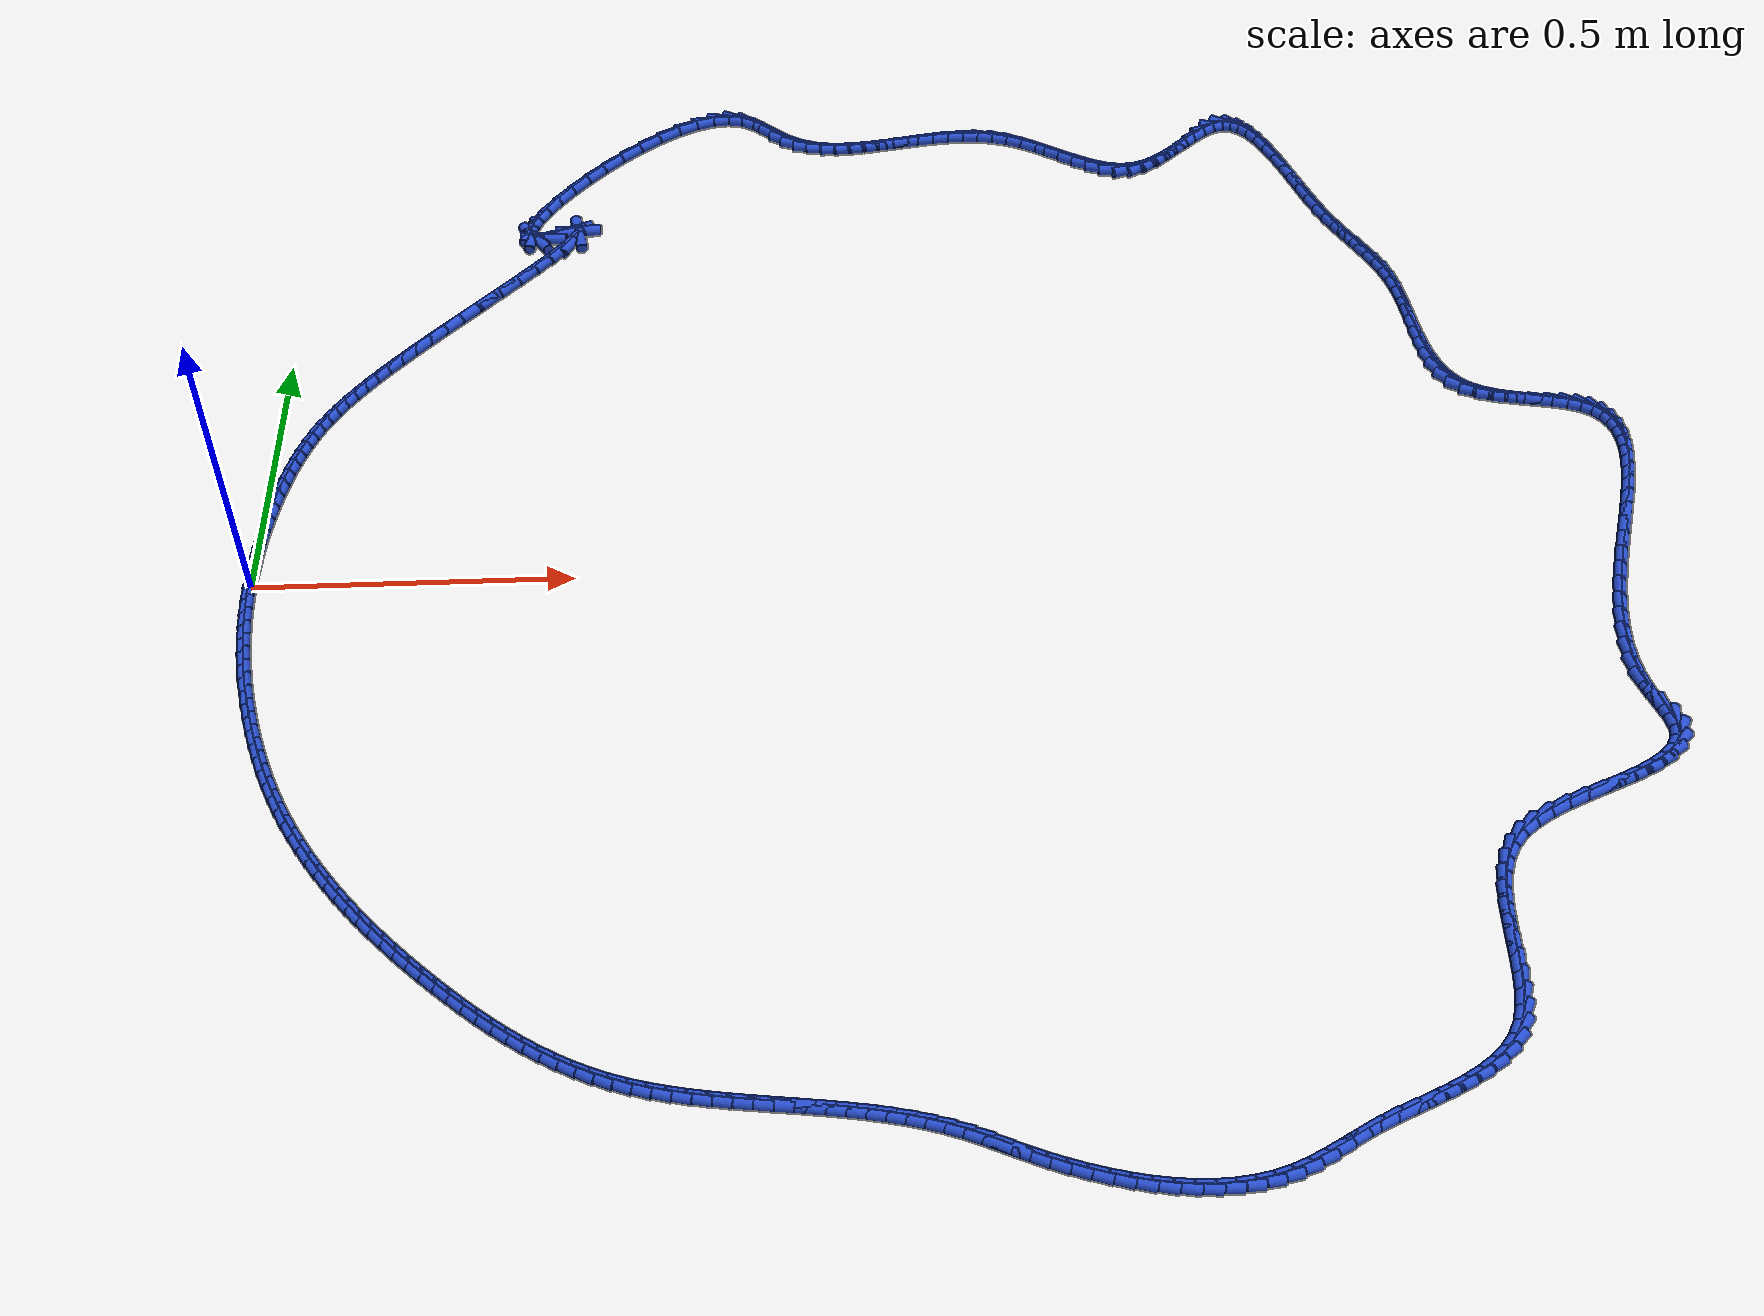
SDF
<sdf version="1.6">
 <world name="default">
  <light name="sun" type="directional">
   <pose>0 0 10 0 -0 0</pose>
   <diffuse>0.8 0.8 0.8 1</diffuse>
   <specular>0.2 0.2 0.2 1</specular>
   <attenuation>
    <range>1000</range>
    <constant>0.9</constant>
    <linear>0.01</linear>
    <quadratic>0.001</quadratic>
   </attenuation>
   <direction>-0.5 0.1 -0.9</direction>
  </light>
  <model name="ground_plane">
   <static>1</static>
   <link name="link">
    <collision name="collision">
     <geometry><plane><normal>0 0 1</normal><size>100 100</size></plane></geometry>
     <surface><friction><ode><mu>100</mu><mu2>50</mu2></ode></friction></surface>
    </collision>
    <visual name="visual">
     <cast_shadows>0</cast_shadows>
     <geometry><plane><normal>0 0 1</normal><size>100 100</size></plane></geometry>
     <material>
      <script><uri>file://media/materials/scripts/gazebo.material</uri><name>Gazebo/WhiteGlow</name></script>
     </material>
    </visual>
   </link>
  </model>
  <gravity>0 0 -9.8</gravity>
  <magnetic_field>6e-06 2.3e-05 -4.2e-05</magnetic_field>
  <atmosphere type="adiabatic"/>
  <physics name="default_physics" default="0" type="ode">
   <max_step_size>0.001</max_step_size>
   <real_time_factor>1</real_time_factor>
   <real_time_update_rate>1000</real_time_update_rate>
  </physics>
  <scene><ambient>0.4 0.4 0.4 1</ambient><background>0.7 0.7 0.7 1</background><shadows>1</shadows></scene>
  <spherical_coordinates>
   <surface_model>EARTH_WGS84</surface_model>
   <latitude_deg>0</latitude_deg>
   <longitude_deg>0</longitude_deg>
   <elevation>0</elevation>
   <heading_deg>0</heading_deg>
  </spherical_coordinates>
  <model name="line">
   <link name="link_0">
    <pose>-8.673617379884035e-19 6.938893903907228e-18 0.01 0 1.57 1.5521254542420253</pose>
    <collision name="collision">
     <geometry><cylinder><radius>0.01</radius><length>0.08</length></cylinder></geometry>
    </collision>
    <visual name="visual">
     <material>
      <script><name>Gazebo/Blue</name><uri>file://media/materials/scripts/gazebo.material</uri></script>
     </material>
     <geometry><cylinder><radius>0.01</radius><length>0.08</length></cylinder></geometry>
    </visual>
   </link>
   <link name="link_1">
    <pose>0.0005129618821565518 0.027470717980359317 0.01 0 1.57 1.5252083230366738</pose>
    <collision name="collision">
     <geometry><cylinder><radius>0.01</radius><length>0.08</length></cylinder></geometry>
    </collision>
    <visual name="visual">
     <material>
      <script><name>Gazebo/Blue</name><uri>file://media/materials/scripts/gazebo.material</uri></script>
     </material>
     <geometry><cylinder><radius>0.01</radius><length>0.08</length></cylinder></geometry>
    </visual>
   </link>
   <link name="link_2">
    <pose>0.0017716657887085212 0.055062007533316366 0.01 0 1.57 1.4994219719318491</pose>
    <collision name="collision">
     <geometry><cylinder><radius>0.01</radius><length>0.08</length></cylinder></geometry>
    </collision>
    <visual name="visual">
     <material>
      <script><name>Gazebo/Blue</name><uri>file://media/materials/scripts/gazebo.material</uri></script>
     </material>
     <geometry><cylinder><radius>0.01</radius><length>0.08</length></cylinder></geometry>
    </visual>
   </link>
   <link name="link_3">
    <pose>0.0037403179978569324 0.08259722112196409 0.01 0 1.57 1.474299678970803</pose>
    <collision name="collision">
     <geometry><cylinder><radius>0.01</radius><length>0.08</length></cylinder></geometry>
    </collision>
    <visual name="visual">
     <material>
      <script><name>Gazebo/Blue</name><uri>file://media/materials/scripts/gazebo.material</uri></script>
     </material>
     <geometry><cylinder><radius>0.01</radius><length>0.08</length></cylinder></geometry>
    </visual>
   </link>
   <link name="link_4">
    <pose>0.006383124787802804 0.10989971120939522 0.01 0 1.57 1.4493886720328548</pose>
    <collision name="collision">
     <geometry><cylinder><radius>0.01</radius><length>0.08</length></cylinder></geometry>
    </collision>
    <visual name="visual">
     <material>
      <script><name>Gazebo/Blue</name><uri>file://media/materials/scripts/gazebo.material</uri></script>
     </material>
     <geometry><cylinder><radius>0.01</radius><length>0.08</length></cylinder></geometry>
    </visual>
   </link>
   <link name="link_5">
    <pose>0.009664292436747157 0.1367928302587027 0.01 0 1.57 1.4242243769494918</pose>
    <collision name="collision">
     <geometry><cylinder><radius>0.01</radius><length>0.08</length></cylinder></geometry>
    </collision>
    <visual name="visual">
     <material>
      <script><name>Gazebo/Blue</name><uri>file://media/materials/scripts/gazebo.material</uri></script>
     </material>
     <geometry><cylinder><radius>0.01</radius><length>0.08</length></cylinder></geometry>
    </visual>
   </link>
   <link name="link_6">
    <pose>0.013548027222891015 0.1630999307329795 0.01 0 1.57 1.3983016234893044</pose>
    <collision name="collision">
     <geometry><cylinder><radius>0.01</radius><length>0.08</length></cylinder></geometry>
    </collision>
    <visual name="visual">
     <material>
      <script><name>Gazebo/Blue</name><uri>file://media/materials/scripts/gazebo.material</uri></script>
     </material>
     <geometry><cylinder><radius>0.01</radius><length>0.08</length></cylinder></geometry>
    </visual>
   </link>
   <link name="link_7">
    <pose>0.0179985354244354 0.18864436509531837 0.01 0 1.57 1.3710390368510565</pose>
    <collision name="collision">
     <geometry><cylinder><radius>0.01</radius><length>0.08</length></cylinder></geometry>
    </collision>
    <visual name="visual">
     <material>
      <script><name>Gazebo/Blue</name><uri>file://media/materials/scripts/gazebo.material</uri></script>
     </material>
     <geometry><cylinder><radius>0.01</radius><length>0.08</length></cylinder></geometry>
    </visual>
   </link>
   <link name="link_8">
    <pose>0.02298002331958133 0.21324948580881228 0.01 0 1.57 1.3417259887913635</pose>
    <collision name="collision">
     <geometry><cylinder><radius>0.01</radius><length>0.08</length></cylinder></geometry>
    </collision>
    <visual name="visual">
     <material>
      <script><name>Gazebo/Blue</name><uri>file://media/materials/scripts/gazebo.material</uri></script>
     </material>
     <geometry><cylinder><radius>0.01</radius><length>0.08</length></cylinder></geometry>
    </visual>
   </link>
   <link name="link_9">
    <pose>0.02845708609574596 0.2367397652805597 0.01 0 1.57 1.3090793507262155</pose>
    <collision name="collision">
     <geometry><cylinder><radius>0.01</radius><length>0.08</length></cylinder></geometry>
    </collision>
    <visual name="visual">
     <material>
      <script><name>Gazebo/Blue</name><uri>file://media/materials/scripts/gazebo.material</uri></script>
     </material>
     <geometry><cylinder><radius>0.01</radius><length>0.08</length></cylinder></geometry>
    </visual>
   </link>
   <link name="link_10">
    <pose>0.03443479503717305 0.2590562351559975 0.01 0 1.57 1.2720951628805037</pose>
    <collision name="collision">
     <geometry><cylinder><radius>0.01</radius><length>0.08</length></cylinder></geometry>
    </collision>
    <visual name="visual">
     <material>
      <script><name>Gazebo/Blue</name><uri>file://media/materials/scripts/gazebo.material</uri></script>
     </material>
     <geometry><cylinder><radius>0.01</radius><length>0.08</length></cylinder></geometry>
    </visual>
   </link>
   <link name="link_11">
    <pose>0.040993519385866366 0.2803567630230828 0.01 0 1.57 1.2312868697705155</pose>
    <collision name="collision">
     <geometry><cylinder><radius>0.01</radius><length>0.08</length></cylinder></geometry>
    </collision>
    <visual name="visual">
     <material>
      <script><name>Gazebo/Blue</name><uri>file://media/materials/scripts/gazebo.material</uri></script>
     </material>
     <geometry><cylinder><radius>0.01</radius><length>0.08</length></cylinder></geometry>
    </visual>
   </link>
   <link name="link_12">
    <pose>0.048221834571035085 0.300822847872139 0.01 0 1.57 1.1876288888675635</pose>
    <collision name="collision">
     <geometry><cylinder><radius>0.01</radius><length>0.08</length></cylinder></geometry>
    </collision>
    <visual name="visual">
     <material>
      <script><name>Gazebo/Blue</name><uri>file://media/materials/scripts/gazebo.material</uri></script>
     </material>
     <geometry><cylinder><radius>0.01</radius><length>0.08</length></cylinder></geometry>
    </visual>
   </link>
   <link name="link_13">
    <pose>0.05620831602188841 0.3206359886934892 0.01 0 1.57 1.1423901993905823</pose>
    <collision name="collision">
     <geometry><cylinder><radius>0.01</radius><length>0.08</length></cylinder></geometry>
    </collision>
    <visual name="visual">
     <material>
      <script><name>Gazebo/Blue</name><uri>file://media/materials/scripts/gazebo.material</uri></script>
     </material>
     <geometry><cylinder><radius>0.01</radius><length>0.08</length></cylinder></geometry>
    </visual>
   </link>
   <link name="link_14">
    <pose>0.06504153916763551 0.3399776844774568 0.01 0 1.57 1.0970109802157728</pose>
    <collision name="collision">
     <geometry><cylinder><radius>0.01</radius><length>0.08</length></cylinder></geometry>
    </collision>
    <visual name="visual">
     <material>
      <script><name>Gazebo/Blue</name><uri>file://media/materials/scripts/gazebo.material</uri></script>
     </material>
     <geometry><cylinder><radius>0.01</radius><length>0.08</length></cylinder></geometry>
    </visual>
   </link>
   <link name="link_15">
    <pose>0.07481007943748563 0.3590294342143652 0.01 0 1.57 1.0529369916706768</pose>
    <collision name="collision">
     <geometry><cylinder><radius>0.01</radius><length>0.08</length></cylinder></geometry>
    </collision>
    <visual name="visual">
     <material>
      <script><name>Gazebo/Blue</name><uri>file://media/materials/scripts/gazebo.material</uri></script>
     </material>
     <geometry><cylinder><radius>0.01</radius><length>0.08</length></cylinder></geometry>
    </visual>
   </link>
   <link name="link_16">
    <pose>0.08560251226064788 0.3779727368945376 0.01 0 1.57 1.0114531920563796</pose>
    <collision name="collision">
     <geometry><cylinder><radius>0.01</radius><length>0.08</length></cylinder></geometry>
    </collision>
    <visual name="visual">
     <material>
      <script><name>Gazebo/Blue</name><uri>file://media/materials/scripts/gazebo.material</uri></script>
     </material>
     <geometry><cylinder><radius>0.01</radius><length>0.08</length></cylinder></geometry>
    </visual>
   </link>
   <link name="link_17">
    <pose>0.09750741306633157 0.3969890915082975 0.01 0 1.57 0.9735583389995821</pose>
    <collision name="collision">
     <geometry><cylinder><radius>0.01</radius><length>0.08</length></cylinder></geometry>
    </collision>
    <visual name="visual">
     <material>
      <script><name>Gazebo/Blue</name><uri>file://media/materials/scripts/gazebo.material</uri></script>
     </material>
     <geometry><cylinder><radius>0.01</radius><length>0.08</length></cylinder></geometry>
    </visual>
   </link>
   <link name="link_18">
    <pose>0.11061335728374573 0.41625999704596794 0.01 0 1.57 0.9399046409608309</pose>
    <collision name="collision">
     <geometry><cylinder><radius>0.01</radius><length>0.08</length></cylinder></geometry>
    </collision>
    <visual name="visual">
     <material>
      <script><name>Gazebo/Blue</name><uri>file://media/materials/scripts/gazebo.material</uri></script>
     </material>
     <geometry><cylinder><radius>0.01</radius><length>0.08</length></cylinder></geometry>
    </visual>
   </link>
   <link name="link_19">
    <pose>0.12500892034209976 0.4359669524978726 0.01 0 1.57 0.9108021718536177</pose>
    <collision name="collision">
     <geometry><cylinder><radius>0.01</radius><length>0.08</length></cylinder></geometry>
    </collision>
    <visual name="visual">
     <material>
      <script><name>Gazebo/Blue</name><uri>file://media/materials/scripts/gazebo.material</uri></script>
     </material>
     <geometry><cylinder><radius>0.01</radius><length>0.08</length></cylinder></geometry>
    </visual>
   </link>
   <link name="link_20">
    <pose>0.14078267767060265 0.4562914568543345 0.01 0 1.57 0.8862697683500474</pose>
    <collision name="collision">
     <geometry><cylinder><radius>0.01</radius><length>0.08</length></cylinder></geometry>
    </collision>
    <visual name="visual">
     <material>
      <script><name>Gazebo/Blue</name><uri>file://media/materials/scripts/gazebo.material</uri></script>
     </material>
     <geometry><cylinder><radius>0.01</radius><length>0.08</length></cylinder></geometry>
    </visual>
   </link>
   <link name="link_21">
    <pose>0.15802320469846376 0.47741500910567725 0.01 0 1.57 0.8661082558374449</pose>
    <collision name="collision">
     <geometry><cylinder><radius>0.01</radius><length>0.08</length></cylinder></geometry>
    </collision>
    <visual name="visual">
     <material>
      <script><name>Gazebo/Blue</name><uri>file://media/materials/scripts/gazebo.material</uri></script>
     </material>
     <geometry><cylinder><radius>0.01</radius><length>0.08</length></cylinder></geometry>
    </visual>
   </link>
   <link name="link_22">
    <pose>0.17681907685489212 0.49951910824222373 0.01 0 1.57 0.8499757122957151</pose>
    <collision name="collision">
     <geometry><cylinder><radius>0.01</radius><length>0.08</length></cylinder></geometry>
    </collision>
    <visual name="visual">
     <material>
      <script><name>Gazebo/Blue</name><uri>file://media/materials/scripts/gazebo.material</uri></script>
     </material>
     <geometry><cylinder><radius>0.01</radius><length>0.08</length></cylinder></geometry>
    </visual>
   </link>
   <link name="link_23">
    <pose>0.19725886956909705 0.5227852532542978 0.01 0 1.57 0.837452380820657</pose>
    <collision name="collision">
     <geometry><cylinder><radius>0.01</radius><length>0.08</length></cylinder></geometry>
    </collision>
    <visual name="visual">
     <material>
      <script><name>Gazebo/Blue</name><uri>file://media/materials/scripts/gazebo.material</uri></script>
     </material>
     <geometry><cylinder><radius>0.01</radius><length>0.08</length></cylinder></geometry>
    </visual>
   </link>
   <link name="link_24">
    <pose>0.21943115827028775 0.5473949431322225 0.01 0 1.57 0.8280902414055195</pose>
    <collision name="collision">
     <geometry><cylinder><radius>0.01</radius><length>0.08</length></cylinder></geometry>
    </collision>
    <visual name="visual">
     <material>
      <script><name>Gazebo/Blue</name><uri>file://media/materials/scripts/gazebo.material</uri></script>
     </material>
     <geometry><cylinder><radius>0.01</radius><length>0.08</length></cylinder></geometry>
    </visual>
   </link>
   <link name="link_25">
    <pose>0.24342451838767332 0.5735296768663212 0.01 0 1.57 0.8214472053036344</pose>
    <collision name="collision">
     <geometry><cylinder><radius>0.01</radius><length>0.08</length></cylinder></geometry>
    </collision>
    <visual name="visual">
     <material>
      <script><name>Gazebo/Blue</name><uri>file://media/materials/scripts/gazebo.material</uri></script>
     </material>
     <geometry><cylinder><radius>0.01</radius><length>0.08</length></cylinder></geometry>
    </visual>
   </link>
   <link name="link_26">
    <pose>0.269327525350463 0.6013709534469172 0.01 0 1.57 0.8171083670340303</pose>
    <collision name="collision">
     <geometry><cylinder><radius>0.01</radius><length>0.08</length></cylinder></geometry>
    </collision>
    <visual name="visual">
     <material>
      <script><name>Gazebo/Blue</name><uri>file://media/materials/scripts/gazebo.material</uri></script>
     </material>
     <geometry><cylinder><radius>0.01</radius><length>0.08</length></cylinder></geometry>
    </visual>
   </link>
   <link name="link_27">
    <pose>0.297228754587866 0.6311002718643337 0.01 0 1.57 0.8151990248766365</pose>
    <collision name="collision">
     <geometry><cylinder><radius>0.01</radius><length>0.08</length></cylinder></geometry>
    </collision>
    <visual name="visual">
     <material>
      <script><name>Gazebo/Blue</name><uri>file://media/materials/scripts/gazebo.material</uri></script>
     </material>
     <geometry><cylinder><radius>0.01</radius><length>0.08</length></cylinder></geometry>
    </visual>
   </link>
   <link name="link_28">
    <pose>0.32703689831106086 0.6627401622242945 0.01 0 1.57 0.8184666140518158</pose>
    <collision name="collision">
     <geometry><cylinder><radius>0.01</radius><length>0.08</length></cylinder></geometry>
    </collision>
    <visual name="visual">
     <material>
      <script><name>Gazebo/Blue</name><uri>file://media/materials/scripts/gazebo.material</uri></script>
     </material>
     <geometry><cylinder><radius>0.01</radius><length>0.08</length></cylinder></geometry>
    </visual>
   </link>
   <link name="link_29">
    <pose>0.35749871417827467 0.6952863137638601 0.01 0 1.57 0.828332748021659</pose>
    <collision name="collision">
     <geometry><cylinder><radius>0.01</radius><length>0.08</length></cylinder></geometry>
    </collision>
    <visual name="visual">
     <material>
      <script><name>Gazebo/Blue</name><uri>file://media/materials/scripts/gazebo.material</uri></script>
     </material>
     <geometry><cylinder><radius>0.01</radius><length>0.08</length></cylinder></geometry>
    </visual>
   </link>
   <link name="link_30">
    <pose>0.38689919114865956 0.7273263351006837 0.01 0 1.57 0.8469575586449529</pose>
    <collision name="collision">
     <geometry><cylinder><radius>0.01</radius><length>0.08</length></cylinder></geometry>
    </collision>
    <visual name="visual">
     <material>
      <script><name>Gazebo/Blue</name><uri>file://media/materials/scripts/gazebo.material</uri></script>
     </material>
     <geometry><cylinder><radius>0.01</radius><length>0.08</length></cylinder></geometry>
    </visual>
   </link>
   <link name="link_31">
    <pose>0.41352214316438013 0.757446796450159 0.01 0 1.57 0.8803396599835526</pose>
    <collision name="collision">
     <geometry><cylinder><radius>0.01</radius><length>0.08</length></cylinder></geometry>
    </collision>
    <visual name="visual">
     <material>
      <script><name>Gazebo/Blue</name><uri>file://media/materials/scripts/gazebo.material</uri></script>
     </material>
     <geometry><cylinder><radius>0.01</radius><length>0.08</length></cylinder></geometry>
    </visual>
   </link>
   <link name="link_32">
    <pose>0.43565138416760013 0.7842342680276797 0.01 0 1.57 0.9452872435706465</pose>
    <collision name="collision">
     <geometry><cylinder><radius>0.01</radius><length>0.08</length></cylinder></geometry>
    </collision>
    <visual name="visual">
     <material>
      <script><name>Gazebo/Blue</name><uri>file://media/materials/scripts/gazebo.material</uri></script>
     </material>
     <geometry><cylinder><radius>0.01</radius><length>0.08</length></cylinder></geometry>
    </visual>
   </link>
   <link name="link_33">
    <pose>0.45157072810048443 0.8062753200486404 0.01 0 1.57 1.1044995687943102</pose>
    <collision name="collision">
     <geometry><cylinder><radius>0.01</radius><length>0.08</length></cylinder></geometry>
    </collision>
    <visual name="visual">
     <material>
      <script><name>Gazebo/Blue</name><uri>file://media/materials/scripts/gazebo.material</uri></script>
     </material>
     <geometry><cylinder><radius>0.01</radius><length>0.08</length></cylinder></geometry>
    </visual>
   </link>
   <link name="link_34">
    <pose>0.4595639889051968 0.8221565227284345 0.01 0 1.57 -1.3748567429442067</pose>
    <collision name="collision">
     <geometry><cylinder><radius>0.01</radius><length>0.08</length></cylinder></geometry>
    </collision>
    <visual name="visual">
     <material>
      <script><name>Gazebo/Blue</name><uri>file://media/materials/scripts/gazebo.material</uri></script>
     </material>
     <geometry><cylinder><radius>0.01</radius><length>0.08</length></cylinder></geometry>
    </visual>
   </link>
   <link name="link_35">
    <pose>0.45791498052390206 0.8304644462824562 0.01 0 1.57 0.05213700567528619</pose>
    <collision name="collision">
     <geometry><cylinder><radius>0.01</radius><length>0.08</length></cylinder></geometry>
    </collision>
    <visual name="visual">
     <material>
      <script><name>Gazebo/Blue</name><uri>file://media/materials/scripts/gazebo.material</uri></script>
     </material>
     <geometry><cylinder><radius>0.01</radius><length>0.08</length></cylinder></geometry>
    </visual>
   </link>
   <link name="link_36">
    <pose>0.44490751689876434 0.8297856609260998 0.01 0 1.57 0.36840967335424907</pose>
    <collision name="collision">
     <geometry><cylinder><radius>0.01</radius><length>0.08</length></cylinder></geometry>
    </collision>
    <visual name="visual">
     <material>
      <script><name>Gazebo/Blue</name><uri>file://media/materials/scripts/gazebo.material</uri></script>
     </material>
     <geometry><cylinder><radius>0.01</radius><length>0.08</length></cylinder></geometry>
    </visual>
   </link>
   <link name="link_37">
    <pose>0.4208996785376612 0.8205178018622584 0.01 0 1.57 0.3027284951760322</pose>
    <collision name="collision">
     <geometry><cylinder><radius>0.01</radius><length>0.08</length></cylinder></geometry>
    </collision>
    <visual name="visual">
     <material>
      <script><name>Gazebo/Blue</name><uri>file://media/materials/scripts/gazebo.material</uri></script>
     </material>
     <geometry><cylinder><radius>0.01</radius><length>0.08</length></cylinder></geometry>
    </visual>
   </link>
   <link name="link_38">
    <pose>0.39811414121544625 0.8134012322591945 0.01 0 1.57 -0.08041300221350424</pose>
    <collision name="collision">
     <geometry><cylinder><radius>0.01</radius><length>0.08</length></cylinder></geometry>
    </collision>
    <visual name="visual">
     <material>
      <script><name>Gazebo/Blue</name><uri>file://media/materials/scripts/gazebo.material</uri></script>
     </material>
     <geometry><cylinder><radius>0.01</radius><length>0.08</length></cylinder></geometry>
    </visual>
   </link>
   <link name="link_39">
    <pose>0.3837821628271969 0.8145562001803319 0.01 0 1.57 -0.9313959087975537</pose>
    <collision name="collision">
     <geometry><cylinder><radius>0.01</radius><length>0.08</length></cylinder></geometry>
    </collision>
    <visual name="visual">
     <material>
      <script><name>Gazebo/Blue</name><uri>file://media/materials/scripts/gazebo.material</uri></script>
     </material>
     <geometry><cylinder><radius>0.01</radius><length>0.08</length></cylinder></geometry>
    </visual>
   </link>
   <link name="link_40">
    <pose>0.3774000783011681 0.8231387433879545 0.01 0 1.57 1.5144169045270115</pose>
    <collision name="collision">
     <geometry><cylinder><radius>0.01</radius><length>0.08</length></cylinder></geometry>
    </collision>
    <visual name="visual">
     <material>
      <script><name>Gazebo/Blue</name><uri>file://media/materials/scripts/gazebo.material</uri></script>
     </material>
     <geometry><cylinder><radius>0.01</radius><length>0.08</length></cylinder></geometry>
    </visual>
   </link>
   <link name="link_41">
    <pose>0.378244899882325 0.838107436393058 0.01 0 1.57 1.2236766655507594</pose>
    <collision name="collision">
     <geometry><cylinder><radius>0.01</radius><length>0.08</length></cylinder></geometry>
    </collision>
    <visual name="visual">
     <material>
      <script><name>Gazebo/Blue</name><uri>file://media/materials/scripts/gazebo.material</uri></script>
     </material>
     <geometry><cylinder><radius>0.01</radius><length>0.08</length></cylinder></geometry>
    </visual>
   </link>
   <link name="link_42">
    <pose>0.3855936398156329 0.8584208537066389 0.01 0 1.57 1.0808151144437264</pose>
    <collision name="collision">
     <geometry><cylinder><radius>0.01</radius><length>0.08</length></cylinder></geometry>
    </collision>
    <visual name="visual">
     <material>
      <script><name>Gazebo/Blue</name><uri>file://media/materials/scripts/gazebo.material</uri></script>
     </material>
     <geometry><cylinder><radius>0.01</radius><length>0.08</length></cylinder></geometry>
    </visual>
   </link>
   <link name="link_43">
    <pose>0.398723310346057 0.8830375698396937 0.01 0 1.57 0.9927453062769094</pose>
    <collision name="collision">
     <geometry><cylinder><radius>0.01</radius><length>0.08</length></cylinder></geometry>
    </collision>
    <visual name="visual">
     <material>
      <script><name>Gazebo/Blue</name><uri>file://media/materials/scripts/gazebo.material</uri></script>
     </material>
     <geometry><cylinder><radius>0.01</radius><length>0.08</length></cylinder></geometry>
    </visual>
   </link>
   <link name="link_44">
    <pose>0.41691092371856275 0.9109161593032189 0.01 0 1.57 0.9283956316620934</pose>
    <collision name="collision">
     <geometry><cylinder><radius>0.01</radius><length>0.08</length></cylinder></geometry>
    </collision>
    <visual name="visual">
     <material>
      <script><name>Gazebo/Blue</name><uri>file://media/materials/scripts/gazebo.material</uri></script>
     </material>
     <geometry><cylinder><radius>0.01</radius><length>0.08</length></cylinder></geometry>
    </visual>
   </link>
   <link name="link_45">
    <pose>0.43943349217811545 0.9410151966082106 0.01 0 1.57 0.8747483978188774</pose>
    <collision name="collision">
     <geometry><cylinder><radius>0.01</radius><length>0.08</length></cylinder></geometry>
    </collision>
    <visual name="visual">
     <material>
      <script><name>Gazebo/Blue</name><uri>file://media/materials/scripts/gazebo.material</uri></script>
     </material>
     <geometry><cylinder><radius>0.01</radius><length>0.08</length></cylinder></geometry>
    </visual>
   </link>
   <link name="link_46">
    <pose>0.46556802796967983 0.9722932562656652 0.01 0 1.57 0.8249568326542357</pose>
    <collision name="collision">
     <geometry><cylinder><radius>0.01</radius><length>0.08</length></cylinder></geometry>
    </collision>
    <visual name="visual">
     <material>
      <script><name>Gazebo/Blue</name><uri>file://media/materials/scripts/gazebo.material</uri></script>
     </material>
     <geometry><cylinder><radius>0.01</radius><length>0.08</length></cylinder></geometry>
    </visual>
   </link>
   <link name="link_47">
    <pose>0.4945915433382219 1.0037089127865793 0.01 0 1.57 0.7744153856924035</pose>
    <collision name="collision">
     <geometry><cylinder><radius>0.01</radius><length>0.08</length></cylinder></geometry>
    </collision>
    <visual name="visual">
     <material>
      <script><name>Gazebo/Blue</name><uri>file://media/materials/scripts/gazebo.material</uri></script>
     </material>
     <geometry><cylinder><radius>0.01</radius><length>0.08</length></cylinder></geometry>
    </visual>
   </link>
   <link name="link_48">
    <pose>0.5257810505287068 1.0342207406819495 0.01 0 1.57 0.7190577772713621</pose>
    <collision name="collision">
     <geometry><cylinder><radius>0.01</radius><length>0.08</length></cylinder></geometry>
    </collision>
    <visual name="visual">
     <material>
      <script><name>Gazebo/Blue</name><uri>file://media/materials/scripts/gazebo.material</uri></script>
     </material>
     <geometry><cylinder><radius>0.01</radius><length>0.08</length></cylinder></geometry>
    </visual>
   </link>
   <link name="link_49">
    <pose>0.5584135617860995 1.0627873144627715 0.01 0 1.57 0.6542644153882542</pose>
    <collision name="collision">
     <geometry><cylinder><radius>0.01</radius><length>0.08</length></cylinder></geometry>
    </collision>
    <visual name="visual">
     <material>
      <script><name>Gazebo/Blue</name><uri>file://media/materials/scripts/gazebo.material</uri></script>
     </material>
     <geometry><cylinder><radius>0.01</radius><length>0.08</length></cylinder></geometry>
    </visual>
   </link>
   <link name="link_50">
    <pose>0.5917660893553653 1.0883672086400424 0.01 0 1.57 0.57372685022199</pose>
    <collision name="collision">
     <geometry><cylinder><radius>0.01</radius><length>0.08</length></cylinder></geometry>
    </collision>
    <visual name="visual">
     <material>
      <script><name>Gazebo/Blue</name><uri>file://media/materials/scripts/gazebo.material</uri></script>
     </material>
     <geometry><cylinder><radius>0.01</radius><length>0.08</length></cylinder></geometry>
    </visual>
   </link>
   <link name="link_51">
    <pose>0.6251156454814695 1.109918997724758 0.01 0 1.57 0.4678189094470453</pose>
    <collision name="collision">
     <geometry><cylinder><radius>0.01</radius><length>0.08</length></cylinder></geometry>
    </collision>
    <visual name="visual">
     <material>
      <script><name>Gazebo/Blue</name><uri>file://media/materials/scripts/gazebo.material</uri></script>
     </material>
     <geometry><cylinder><radius>0.01</radius><length>0.08</length></cylinder></geometry>
    </visual>
   </link>
   <link name="link_52">
    <pose>0.6577392424093775 1.126401256227915 0.01 0 1.57 0.3211659014063102</pose>
    <collision name="collision">
     <geometry><cylinder><radius>0.01</radius><length>0.08</length></cylinder></geometry>
    </collision>
    <visual name="visual">
     <material>
      <script><name>Gazebo/Blue</name><uri>file://media/materials/scripts/gazebo.material</uri></script>
     </material>
     <geometry><cylinder><radius>0.01</radius><length>0.08</length></cylinder></geometry>
    </visual>
   </link>
   <link name="link_53">
    <pose>0.6889138923840548 1.13677255866051 0.01 0 1.57 0.11053450320210302</pose>
    <collision name="collision">
     <geometry><cylinder><radius>0.01</radius><length>0.08</length></cylinder></geometry>
    </collision>
    <visual name="visual">
     <material>
      <script><name>Gazebo/Blue</name><uri>file://media/materials/scripts/gazebo.material</uri></script>
     </material>
     <geometry><cylinder><radius>0.01</radius><length>0.08</length></cylinder></geometry>
    </visual>
   </link>
   <link name="link_54">
    <pose>0.7179166076504662 1.139991479533539 0.01 0 1.57 -0.18571488944040304</pose>
    <collision name="collision">
     <geometry><cylinder><radius>0.01</radius><length>0.08</length></cylinder></geometry>
    </collision>
    <visual name="visual">
     <material>
      <script><name>Gazebo/Blue</name><uri>file://media/materials/scripts/gazebo.material</uri></script>
     </material>
     <geometry><cylinder><radius>0.01</radius><length>0.08</length></cylinder></geometry>
    </visual>
   </link>
   <link name="link_55">
    <pose>0.7440522048131548 1.1350811270457015 0.01 0 1.57 -0.48040268974108447</pose>
    <collision name="collision">
     <geometry><cylinder><radius>0.01</radius><length>0.08</length></cylinder></geometry>
    </collision>
    <visual name="visual">
     <material>
      <script><name>Gazebo/Blue</name><uri>file://media/materials/scripts/gazebo.material</uri></script>
     </material>
     <geometry><cylinder><radius>0.01</radius><length>0.08</length></cylinder></geometry>
    </visual>
   </link>
   <link name="link_56">
    <pose>0.7674182408719596 1.1229045532705673 0.01 0 1.57 -0.6532284142592251</pose>
    <collision name="collision">
     <geometry><cylinder><radius>0.01</radius><length>0.08</length></cylinder></geometry>
    </collision>
    <visual name="visual">
     <material>
      <script><name>Gazebo/Blue</name><uri>file://media/materials/scripts/gazebo.material</uri></script>
     </material>
     <geometry><cylinder><radius>0.01</radius><length>0.08</length></cylinder></geometry>
    </visual>
   </link>
   <link name="link_57">
    <pose>0.7890008345854099 1.1063871547453505 0.01 0 1.57 -0.7077223486076931</pose>
    <collision name="collision">
     <geometry><cylinder><radius>0.01</radius><length>0.08</length></cylinder></geometry>
    </collision>
    <visual name="visual">
     <material>
      <script><name>Gazebo/Blue</name><uri>file://media/materials/scripts/gazebo.material</uri></script>
     </material>
     <geometry><cylinder><radius>0.01</radius><length>0.08</length></cylinder></geometry>
    </visual>
   </link>
   <link name="link_58">
    <pose>0.8098331516015134 1.0885635234470856 0.01 0 1.57 -0.651301326150636</pose>
    <collision name="collision">
     <geometry><cylinder><radius>0.01</radius><length>0.08</length></cylinder></geometry>
    </collision>
    <visual name="visual">
     <material>
      <script><name>Gazebo/Blue</name><uri>file://media/materials/scripts/gazebo.material</uri></script>
     </material>
     <geometry><cylinder><radius>0.01</radius><length>0.08</length></cylinder></geometry>
    </visual>
   </link>
   <link name="link_59">
    <pose>0.8309483573628698 1.0724682507121002 0.01 0 1.57 -0.49337258095488196</pose>
    <collision name="collision">
     <geometry><cylinder><radius>0.01</radius><length>0.08</length></cylinder></geometry>
    </collision>
    <visual name="visual">
     <material>
      <script><name>Gazebo/Blue</name><uri>file://media/materials/scripts/gazebo.material</uri></script>
     </material>
     <geometry><cylinder><radius>0.01</radius><length>0.08</length></cylinder></geometry>
    </visual>
   </link>
   <link name="link_60">
    <pose>0.8531801064048204 1.060513615424768 0.01 0 1.57 -0.32226206378518746</pose>
    <collision name="collision">
     <geometry><cylinder><radius>0.01</radius><length>0.08</length></cylinder></geometry>
    </collision>
    <visual name="visual">
     <material>
      <script><name>Gazebo/Blue</name><uri>file://media/materials/scripts/gazebo.material</uri></script>
     </material>
     <geometry><cylinder><radius>0.01</radius><length>0.08</length></cylinder></geometry>
    </visual>
   </link>
   <link name="link_61">
    <pose>0.8765880582233905 1.0526976587852286 0.01 0 1.57 -0.17264172392268098</pose>
    <collision name="collision">
     <geometry><cylinder><radius>0.01</radius><length>0.08</length></cylinder></geometry>
    </collision>
    <visual name="visual">
     <material>
      <script><name>Gazebo/Blue</name><uri>file://media/materials/scripts/gazebo.material</uri></script>
     </material>
     <geometry><cylinder><radius>0.01</radius><length>0.08</length></cylinder></geometry>
    </visual>
   </link>
   <link name="link_62">
    <pose>0.9010442055997253 1.0484330538295867 0.01 0 1.57 -0.051206891379099624</pose>
    <collision name="collision">
     <geometry><cylinder><radius>0.01</radius><length>0.08</length></cylinder></geometry>
    </collision>
    <visual name="visual">
     <material>
      <script><name>Gazebo/Blue</name><uri>file://media/materials/scripts/gazebo.material</uri></script>
     </material>
     <geometry><cylinder><radius>0.01</radius><length>0.08</length></cylinder></geometry>
    </visual>
   </link>
   <link name="link_63">
    <pose>0.9264205413149719 1.047132473593947 0.01 0 1.57 0.04109944578978239</pose>
    <collision name="collision">
     <geometry><cylinder><radius>0.01</radius><length>0.08</length></cylinder></geometry>
    </collision>
    <visual name="visual">
     <material>
      <script><name>Gazebo/Blue</name><uri>file://media/materials/scripts/gazebo.material</uri></script>
     </material>
     <geometry><cylinder><radius>0.01</radius><length>0.08</length></cylinder></geometry>
    </visual>
   </link>
   <link name="link_64">
    <pose>0.9525890581502746 1.048208591114413 0.01 0 1.57 0.10638773826787151</pose>
    <collision name="collision">
     <geometry><cylinder><radius>0.01</radius><length>0.08</length></cylinder></geometry>
    </collision>
    <visual name="visual">
     <material>
      <script><name>Gazebo/Blue</name><uri>file://media/materials/scripts/gazebo.material</uri></script>
     </material>
     <geometry><cylinder><radius>0.01</radius><length>0.08</length></cylinder></geometry>
    </visual>
   </link>
   <link name="link_65">
    <pose>0.9794217488867801 1.0510740794270903 0.01 0 1.57 0.1475390606556527</pose>
    <collision name="collision">
     <geometry><cylinder><radius>0.01</radius><length>0.08</length></cylinder></geometry>
    </collision>
    <visual name="visual">
     <material>
      <script><name>Gazebo/Blue</name><uri>file://media/materials/scripts/gazebo.material</uri></script>
     </material>
     <geometry><cylinder><radius>0.01</radius><length>0.08</length></cylinder></geometry>
    </visual>
   </link>
   <link name="link_66">
    <pose>1.0067906063056338 1.0551416115680825 0.01 0 1.57 0.16699569944765041</pose>
    <collision name="collision">
     <geometry><cylinder><radius>0.01</radius><length>0.08</length></cylinder></geometry>
    </collision>
    <visual name="visual">
     <material>
      <script><name>Gazebo/Blue</name><uri>file://media/materials/scripts/gazebo.material</uri></script>
     </material>
     <geometry><cylinder><radius>0.01</radius><length>0.08</length></cylinder></geometry>
    </visual>
   </link>
   <link name="link_67">
    <pose>1.0345676231879817 1.0598238605734944 0.01 0 1.57 0.16630823327488306</pose>
    <collision name="collision">
     <geometry><cylinder><radius>0.01</radius><length>0.08</length></cylinder></geometry>
    </collision>
    <visual name="visual">
     <material>
      <script><name>Gazebo/Blue</name><uri>file://media/materials/scripts/gazebo.material</uri></script>
     </material>
     <geometry><cylinder><radius>0.01</radius><length>0.08</length></cylinder></geometry>
    </visual>
   </link>
   <link name="link_68">
    <pose>1.0626247923149699 1.0645334994794307 0.01 0 1.57 0.14605643918004574</pose>
    <collision name="collision">
     <geometry><cylinder><radius>0.01</radius><length>0.08</length></cylinder></geometry>
    </collision>
    <visual name="visual">
     <material>
      <script><name>Gazebo/Blue</name><uri>file://media/materials/scripts/gazebo.material</uri></script>
     </material>
     <geometry><cylinder><radius>0.01</radius><length>0.08</length></cylinder></geometry>
    </visual>
   </link>
   <link name="link_69">
    <pose>1.0908341064677438 1.0686832013219956 0.01 0 1.57 0.10594510084303424</pose>
    <collision name="collision">
     <geometry><cylinder><radius>0.01</radius><length>0.08</length></cylinder></geometry>
    </collision>
    <visual name="visual">
     <material>
      <script><name>Gazebo/Blue</name><uri>file://media/materials/scripts/gazebo.material</uri></script>
     </material>
     <geometry><cylinder><radius>0.01</radius><length>0.08</length></cylinder></geometry>
    </visual>
   </link>
   <link name="link_70">
    <pose>1.1190675584274488 1.0716856391372933 0.01 0 1.57 0.045041171255095575</pose>
    <collision name="collision">
     <geometry><cylinder><radius>0.01</radius><length>0.08</length></cylinder></geometry>
    </collision>
    <visual name="visual">
     <material>
      <script><name>Gazebo/Blue</name><uri>file://media/materials/scripts/gazebo.material</uri></script>
     </material>
     <geometry><cylinder><radius>0.01</radius><length>0.08</length></cylinder></geometry>
    </visual>
   </link>
   <link name="link_71">
    <pose>1.1471971409752317 1.0729534859614287 0.01 0 1.57 -0.03776546968417546</pose>
    <collision name="collision">
     <geometry><cylinder><radius>0.01</radius><length>0.08</length></cylinder></geometry>
    </collision>
    <visual name="visual">
     <material>
      <script><name>Gazebo/Blue</name><uri>file://media/materials/scripts/gazebo.material</uri></script>
     </material>
     <geometry><cylinder><radius>0.01</radius><length>0.08</length></cylinder></geometry>
    </visual>
   </link>
   <link name="link_72">
    <pose>1.1750948468922375 1.0718994148305059 0.01 0 1.57 -0.14294108561909138</pose>
    <collision name="collision">
     <geometry><cylinder><radius>0.01</radius><length>0.08</length></cylinder></geometry>
    </collision>
    <visual name="visual">
     <material>
      <script><name>Gazebo/Blue</name><uri>file://media/materials/scripts/gazebo.material</uri></script>
     </material>
     <geometry><cylinder><radius>0.01</radius><length>0.08</length></cylinder></geometry>
    </visual>
   </link>
   <link name="link_73">
    <pose>1.202632668959613 1.06793609878063 0.01 0 1.57 -0.26894906797217144</pose>
    <collision name="collision">
     <geometry><cylinder><radius>0.01</radius><length>0.08</length></cylinder></geometry>
    </collision>
    <visual name="visual">
     <material>
      <script><name>Gazebo/Blue</name><uri>file://media/materials/scripts/gazebo.material</uri></script>
     </material>
     <geometry><cylinder><radius>0.01</radius><length>0.08</length></cylinder></geometry>
    </visual>
   </link>
   <link name="link_74">
    <pose>1.2296830183890382 1.060480291139011 0.01 0 1.57 -0.39330779206226607</pose>
    <collision name="collision">
     <geometry><cylinder><radius>0.01</radius><length>0.08</length></cylinder></geometry>
    </collision>
    <visual name="visual">
     <material>
      <script><name>Gazebo/Blue</name><uri>file://media/materials/scripts/gazebo.material</uri></script>
     </material>
     <geometry><cylinder><radius>0.01</radius><length>0.08</length></cylinder></geometry>
    </visual>
   </link>
   <link name="link_75">
    <pose>1.2561736688695626 1.0494886078980596 0.01 0 1.57 -0.4793022470671209</pose>
    <collision name="collision">
     <geometry><cylinder><radius>0.01</radius><length>0.08</length></cylinder></geometry>
    </collision>
    <visual name="visual">
     <material>
      <script><name>Gazebo/Blue</name><uri>file://media/materials/scripts/gazebo.material</uri></script>
     </material>
     <geometry><cylinder><radius>0.01</radius><length>0.08</length></cylinder></geometry>
    </visual>
   </link>
   <link name="link_76">
    <pose>1.2821425605165808 1.035991943936735 0.01 0 1.57 -0.5271888174598964</pose>
    <collision name="collision">
     <geometry><cylinder><radius>0.01</radius><length>0.08</length></cylinder></geometry>
    </collision>
    <visual name="visual">
     <material>
      <script><name>Gazebo/Blue</name><uri>file://media/materials/scripts/gazebo.material</uri></script>
     </material>
     <geometry><cylinder><radius>0.01</radius><length>0.08</length></cylinder></geometry>
    </visual>
   </link>
   <link name="link_77">
    <pose>1.3076406678835422 1.0211482983894755 0.01 0 1.57 -0.5399986357784393</pose>
    <collision name="collision">
     <geometry><cylinder><radius>0.01</radius><length>0.08</length></cylinder></geometry>
    </collision>
    <visual name="visual">
     <material>
      <script><name>Gazebo/Blue</name><uri>file://media/materials/scripts/gazebo.material</uri></script>
     </material>
     <geometry><cylinder><radius>0.01</radius><length>0.08</length></cylinder></geometry>
    </visual>
   </link>
   <link name="link_78">
    <pose>1.3327189655238965 1.0061156703907195 0.01 0 1.57 -0.5174334839989857</pose>
    <collision name="collision">
     <geometry><cylinder><radius>0.01</radius><length>0.08</length></cylinder></geometry>
    </collision>
    <visual name="visual">
     <material>
      <script><name>Gazebo/Blue</name><uri>file://media/materials/scripts/gazebo.material</uri></script>
     </material>
     <geometry><cylinder><radius>0.01</radius><length>0.08</length></cylinder></geometry>
    </visual>
   </link>
   <link name="link_79">
    <pose>1.3574284279910924 0.9920520590749053 0.01 0 1.57 -0.4551100600985925</pose>
    <collision name="collision">
     <geometry><cylinder><radius>0.01</radius><length>0.08</length></cylinder></geometry>
    </collision>
    <visual name="visual">
     <material>
      <script><name>Gazebo/Blue</name><uri>file://media/materials/scripts/gazebo.material</uri></script>
     </material>
     <geometry><cylinder><radius>0.01</radius><length>0.08</length></cylinder></geometry>
    </visual>
   </link>
   <link name="link_80">
    <pose>1.381820029838579 0.9801154635764713 0.01 0 1.57 -0.3443324530920283</pose>
    <collision name="collision">
     <geometry><cylinder><radius>0.01</radius><length>0.08</length></cylinder></geometry>
    </collision>
    <visual name="visual">
     <material>
      <script><name>Gazebo/Blue</name><uri>file://media/materials/scripts/gazebo.material</uri></script>
     </material>
     <geometry><cylinder><radius>0.01</radius><length>0.08</length></cylinder></geometry>
    </visual>
   </link>
   <link name="link_81">
    <pose>1.4059447456198064 0.9714638830298553 0.01 0 1.57 -0.17424081367749977</pose>
    <collision name="collision">
     <geometry><cylinder><radius>0.01</radius><length>0.08</length></cylinder></geometry>
    </collision>
    <visual name="visual">
     <material>
      <script><name>Gazebo/Blue</name><uri>file://media/materials/scripts/gazebo.material</uri></script>
     </material>
     <geometry><cylinder><radius>0.01</radius><length>0.08</length></cylinder></geometry>
    </visual>
   </link>
   <link name="link_82">
    <pose>1.4298535498882234 0.9672553165694961 0.01 0 1.57 0.05857738921441904</pose>
    <collision name="collision">
     <geometry><cylinder><radius>0.01</radius><length>0.08</length></cylinder></geometry>
    </collision>
    <visual name="visual">
     <material>
      <script><name>Gazebo/Blue</name><uri>file://media/materials/scripts/gazebo.material</uri></script>
     </material>
     <geometry><cylinder><radius>0.01</radius><length>0.08</length></cylinder></geometry>
    </visual>
   </link>
   <link name="link_83">
    <pose>1.4535974171972794 0.9686477633298317 0.01 0 1.57 0.3290535102537519</pose>
    <collision name="collision">
     <geometry><cylinder><radius>0.01</radius><length>0.08</length></cylinder></geometry>
    </collision>
    <visual name="visual">
     <material>
      <script><name>Gazebo/Blue</name><uri>file://media/materials/scripts/gazebo.material</uri></script>
     </material>
     <geometry><cylinder><radius>0.01</radius><length>0.08</length></cylinder></geometry>
    </visual>
   </link>
   <link name="link_84">
    <pose>1.4772212800030426 0.9767145488347417 0.01 0 1.57 0.5439208422819638</pose>
    <collision name="collision">
     <geometry><cylinder><radius>0.01</radius><length>0.08</length></cylinder></geometry>
    </collision>
    <visual name="visual">
     <material>
      <script><name>Gazebo/Blue</name><uri>file://media/materials/scripts/gazebo.material</uri></script>
     </material>
     <geometry><cylinder><radius>0.01</radius><length>0.08</length></cylinder></geometry>
    </visual>
   </link>
   <link name="link_85">
    <pose>1.500652777641465 0.9908852594644579 0.01 0 1.57 0.6684980318929817</pose>
    <collision name="collision">
     <geometry><cylinder><radius>0.01</radius><length>0.08</length></cylinder></geometry>
    </collision>
    <visual name="visual">
     <material>
      <script><name>Gazebo/Blue</name><uri>file://media/materials/scripts/gazebo.material</uri></script>
     </material>
     <geometry><cylinder><radius>0.01</radius><length>0.08</length></cylinder></geometry>
    </visual>
   </link>
   <link name="link_86">
    <pose>1.5237131667250068 1.0090986401361108 0.01 0 1.57 0.7299794538144441</pose>
    <collision name="collision">
     <geometry><cylinder><radius>0.01</radius><length>0.08</length></cylinder></geometry>
    </collision>
    <visual name="visual">
     <material>
      <script><name>Gazebo/Blue</name><uri>file://media/materials/scripts/gazebo.material</uri></script>
     </material>
     <geometry><cylinder><radius>0.01</radius><length>0.08</length></cylinder></geometry>
    </visual>
   </link>
   <link name="link_87">
    <pose>1.5462198503705196 1.0292394330975594 0.01 0 1.57 0.7418665057884931</pose>
    <collision name="collision">
     <geometry><cylinder><radius>0.01</radius><length>0.08</length></cylinder></geometry>
    </collision>
    <visual name="visual">
     <material>
      <script><name>Gazebo/Blue</name><uri>file://media/materials/scripts/gazebo.material</uri></script>
     </material>
     <geometry><cylinder><radius>0.01</radius><length>0.08</length></cylinder></geometry>
    </visual>
   </link>
   <link name="link_88">
    <pose>1.5679902316948557 1.0491923805966634 0.01 0 1.57 0.7024324888977352</pose>
    <collision name="collision">
     <geometry><cylinder><radius>0.01</radius><length>0.08</length></cylinder></geometry>
    </collision>
    <visual name="visual">
     <material>
      <script><name>Gazebo/Blue</name><uri>file://media/materials/scripts/gazebo.material</uri></script>
     </material>
     <geometry><cylinder><radius>0.01</radius><length>0.08</length></cylinder></geometry>
    </visual>
   </link>
   <link name="link_89">
    <pose>1.5888417138148654 1.0668422248812817 0.01 0 1.57 0.5902715443844094</pose>
    <collision name="collision">
     <geometry><cylinder><radius>0.01</radius><length>0.08</length></cylinder></geometry>
    </collision>
    <visual name="visual">
     <material>
      <script><name>Gazebo/Blue</name><uri>file://media/materials/scripts/gazebo.material</uri></script>
     </material>
     <geometry><cylinder><radius>0.01</radius><length>0.08</length></cylinder></geometry>
    </visual>
   </link>
   <link name="link_90">
    <pose>1.6085916998474008 1.080073708199273 0.01 0 1.57 0.3479893441711368</pose>
    <collision name="collision">
     <geometry><cylinder><radius>0.01</radius><length>0.08</length></cylinder></geometry>
    </collision>
    <visual name="visual">
     <material>
      <script><name>Gazebo/Blue</name><uri>file://media/materials/scripts/gazebo.material</uri></script>
     </material>
     <geometry><cylinder><radius>0.01</radius><length>0.08</length></cylinder></geometry>
    </visual>
   </link>
   <link name="link_91">
    <pose>1.627057674048823 1.0867722698052826 0.01 0 1.57 -0.07267802041351287</pose>
    <collision name="collision">
     <geometry><cylinder><radius>0.01</radius><length>0.08</length></cylinder></geometry>
    </collision>
    <visual name="visual">
     <material>
      <script><name>Gazebo/Blue</name><uri>file://media/materials/scripts/gazebo.material</uri></script>
     </material>
     <geometry><cylinder><radius>0.01</radius><length>0.08</length></cylinder></geometry>
    </visual>
   </link>
   <link name="link_92">
    <pose>1.6441392229602727 1.085528626192248 0.01 0 1.57 -0.4957483695676413</pose>
    <collision name="collision">
     <geometry><cylinder><radius>0.01</radius><length>0.08</length></cylinder></geometry>
    </collision>
    <visual name="visual">
     <material>
      <script><name>Gazebo/Blue</name><uri>file://media/materials/scripts/gazebo.material</uri></script>
     </material>
     <geometry><cylinder><radius>0.01</radius><length>0.08</length></cylinder></geometry>
    </visual>
   </link>
   <link name="link_93">
    <pose>1.6599725455999281 1.0769660486693442 0.01 0 1.57 -0.7898024223773686</pose>
    <collision name="collision">
     <geometry><cylinder><radius>0.01</radius><length>0.08</length></cylinder></geometry>
    </collision>
    <visual name="visual">
     <material>
      <script><name>Gazebo/Blue</name><uri>file://media/materials/scripts/gazebo.material</uri></script>
     </material>
     <geometry><cylinder><radius>0.01</radius><length>0.08</length></cylinder></geometry>
    </visual>
   </link>
   <link name="link_94">
    <pose>1.6747362093902405 1.0620717627430847 0.01 0 1.57 -0.9699054391754726</pose>
    <collision name="collision">
     <geometry><cylinder><radius>0.01</radius><length>0.08</length></cylinder></geometry>
    </collision>
    <visual name="visual">
     <material>
      <script><name>Gazebo/Blue</name><uri>file://media/materials/scripts/gazebo.material</uri></script>
     </material>
     <geometry><cylinder><radius>0.01</radius><length>0.08</length></cylinder></geometry>
    </visual>
   </link>
   <link name="link_95">
    <pose>1.6886087817536592 1.0418329939199809 0.01 0 1.57 -1.079505201330603</pose>
    <collision name="collision">
     <geometry><cylinder><radius>0.01</radius><length>0.08</length></cylinder></geometry>
    </collision>
    <visual name="visual">
     <material>
      <script><name>Gazebo/Blue</name><uri>file://media/materials/scripts/gazebo.material</uri></script>
     </material>
     <geometry><cylinder><radius>0.01</radius><length>0.08</length></cylinder></geometry>
    </visual>
   </link>
   <link name="link_96">
    <pose>1.7017688301126364 1.0172369677065465 0.01 0 1.57 -1.1467130301496264</pose>
    <collision name="collision">
     <geometry><cylinder><radius>0.01</radius><length>0.08</length></cylinder></geometry>
    </collision>
    <visual name="visual">
     <material>
      <script><name>Gazebo/Blue</name><uri>file://media/materials/scripts/gazebo.material</uri></script>
     </material>
     <geometry><cylinder><radius>0.01</radius><length>0.08</length></cylinder></geometry>
    </visual>
   </link>
   <link name="link_97">
    <pose>1.7143949218896224 0.9892709096092945 0.01 0 1.57 -1.186569959856762</pose>
    <collision name="collision">
     <geometry><cylinder><radius>0.01</radius><length>0.08</length></cylinder></geometry>
    </collision>
    <visual name="visual">
     <material>
      <script><name>Gazebo/Blue</name><uri>file://media/materials/scripts/gazebo.material</uri></script>
     </material>
     <geometry><cylinder><radius>0.01</radius><length>0.08</length></cylinder></geometry>
    </visual>
   </link>
   <link name="link_98">
    <pose>1.7266656245070684 0.9589220451347377 0.01 0 1.57 -1.2067964951865686</pose>
    <collision name="collision">
     <geometry><cylinder><radius>0.01</radius><length>0.08</length></cylinder></geometry>
    </collision>
    <visual name="visual">
     <material>
      <script><name>Gazebo/Blue</name><uri>file://media/materials/scripts/gazebo.material</uri></script>
     </material>
     <geometry><cylinder><radius>0.01</radius><length>0.08</length></cylinder></geometry>
    </visual>
   </link>
   <link name="link_99">
    <pose>1.7387595053874239 0.9271775997893885 0.01 0 1.57 -1.2109810207986353</pose>
    <collision name="collision">
     <geometry><cylinder><radius>0.01</radius><length>0.08</length></cylinder></geometry>
    </collision>
    <visual name="visual">
     <material>
      <script><name>Gazebo/Blue</name><uri>file://media/materials/scripts/gazebo.material</uri></script>
     </material>
     <geometry><cylinder><radius>0.01</radius><length>0.08</length></cylinder></geometry>
    </visual>
   </link>
   <link name="link_100">
    <pose>1.7508551319531414 0.89502479907976 0.01 0 1.57 -1.199982376759034</pose>
    <collision name="collision">
     <geometry><cylinder><radius>0.01</radius><length>0.08</length></cylinder></geometry>
    </collision>
    <visual name="visual">
     <material>
      <script><name>Gazebo/Blue</name><uri>file://media/materials/scripts/gazebo.material</uri></script>
     </material>
     <geometry><cylinder><radius>0.01</radius><length>0.08</length></cylinder></geometry>
    </visual>
   </link>
   <link name="link_101">
    <pose>1.76313107162667 0.8634508685123652 0.01 0 1.57 -1.1722755131791043</pose>
    <collision name="collision">
     <geometry><cylinder><radius>0.01</radius><length>0.08</length></cylinder></geometry>
    </collision>
    <visual name="visual">
     <material>
      <script><name>Gazebo/Blue</name><uri>file://media/materials/scripts/gazebo.material</uri></script>
     </material>
     <geometry><cylinder><radius>0.01</radius><length>0.08</length></cylinder></geometry>
    </visual>
   </link>
   <link name="link_102">
    <pose>1.7757658918304617 0.8334430335937171 0.01 0 1.57 -1.126703625701161</pose>
    <collision name="collision">
     <geometry><cylinder><radius>0.01</radius><length>0.08</length></cylinder></geometry>
    </collision>
    <visual name="visual">
     <material>
      <script><name>Gazebo/Blue</name><uri>file://media/materials/scripts/gazebo.material</uri></script>
     </material>
     <geometry><cylinder><radius>0.01</radius><length>0.08</length></cylinder></geometry>
    </visual>
   </link>
   <link name="link_103">
    <pose>1.7888943279016356 0.8058501116961803 0.01 0 1.57 -1.0830853196525927</pose>
    <collision name="collision">
     <geometry><cylinder><radius>0.01</radius><length>0.08</length></cylinder></geometry>
    </collision>
    <visual name="visual">
     <material>
      <script><name>Gazebo/Blue</name><uri>file://media/materials/scripts/gazebo.material</uri></script>
     </material>
     <geometry><cylinder><radius>0.01</radius><length>0.08</length></cylinder></geometry>
    </visual>
   </link>
   <link name="link_104">
    <pose>1.8023328607881006 0.7805159715144417 0.01 0 1.57 -1.0549644850772484</pose>
    <collision name="collision">
     <geometry><cylinder><radius>0.01</radius><length>0.08</length></cylinder></geometry>
    </collision>
    <visual name="visual">
     <material>
      <script><name>Gazebo/Blue</name><uri>file://media/materials/scripts/gazebo.material</uri></script>
     </material>
     <geometry><cylinder><radius>0.01</radius><length>0.08</length></cylinder></geometry>
    </visual>
   </link>
   <link name="link_105">
    <pose>1.8157575261701608 0.7568409991369649 0.01 0 1.57 -1.0462670902088889</pose>
    <collision name="collision">
     <geometry><cylinder><radius>0.01</radius><length>0.08</length></cylinder></geometry>
    </collision>
    <visual name="visual">
     <material>
      <script><name>Gazebo/Blue</name><uri>file://media/materials/scripts/gazebo.material</uri></script>
     </material>
     <geometry><cylinder><radius>0.01</radius><length>0.08</length></cylinder></geometry>
    </visual>
   </link>
   <link name="link_106">
    <pose>1.8288437429993871 0.7342236332141086 0.01 0 1.57 -1.0598667852115629</pose>
    <collision name="collision">
     <geometry><cylinder><radius>0.01</radius><length>0.08</length></cylinder></geometry>
    </collision>
    <visual name="visual">
     <material>
      <script><name>Gazebo/Blue</name><uri>file://media/materials/scripts/gazebo.material</uri></script>
     </material>
     <geometry><cylinder><radius>0.01</radius><length>0.08</length></cylinder></geometry>
    </visual>
   </link>
   <link name="link_107">
    <pose>1.841266930227349 0.7120623123962305 0.01 0 1.57 -1.0970808396330438</pose>
    <collision name="collision">
     <geometry><cylinder><radius>0.01</radius><length>0.08</length></cylinder></geometry>
    </collision>
    <visual name="visual">
     <material>
      <script><name>Gazebo/Blue</name><uri>file://media/materials/scripts/gazebo.material</uri></script>
     </material>
     <geometry><cylinder><radius>0.01</radius><length>0.08</length></cylinder></geometry>
    </visual>
   </link>
   <link name="link_108">
    <pose>1.8527025068056175 0.6897554753336896 0.01 0 1.57 -1.157028779472535</pose>
    <collision name="collision">
     <geometry><cylinder><radius>0.01</radius><length>0.08</length></cylinder></geometry>
    </collision>
    <visual name="visual">
     <material>
      <script><name>Gazebo/Blue</name><uri>file://media/materials/scripts/gazebo.material</uri></script>
     </material>
     <geometry><cylinder><radius>0.01</radius><length>0.08</length></cylinder></geometry>
    </visual>
   </link>
   <link name="link_109">
    <pose>1.8628258916857634 0.6667015606768443 0.01 0 1.57 -1.2361045497343777</pose>
    <collision name="collision">
     <geometry><cylinder><radius>0.01</radius><length>0.08</length></cylinder></geometry>
    </collision>
    <visual name="visual">
     <material>
      <script><name>Gazebo/Blue</name><uri>file://media/materials/scripts/gazebo.material</uri></script>
     </material>
     <geometry><cylinder><radius>0.01</radius><length>0.08</length></cylinder></geometry>
    </visual>
   </link>
   <link name="link_110">
    <pose>1.8713125038193557 0.6422990070760527 0.01 0 1.57 -1.3240467772435631</pose>
    <collision name="collision">
     <geometry><cylinder><radius>0.01</radius><length>0.08</length></cylinder></geometry>
    </collision>
    <visual name="visual">
     <material>
      <script><name>Gazebo/Blue</name><uri>file://media/materials/scripts/gazebo.material</uri></script>
     </material>
     <geometry><cylinder><radius>0.01</radius><length>0.08</length></cylinder></geometry>
    </visual>
   </link>
   <link name="link_111">
    <pose>1.8779228191657453 0.6160553501578272 0.01 0 1.57 -1.390050520017113</pose>
    <collision name="collision">
     <geometry><cylinder><radius>0.01</radius><length>0.08</length></cylinder></geometry>
    </collision>
    <visual name="visual">
     <material>
      <script><name>Gazebo/Blue</name><uri>file://media/materials/scripts/gazebo.material</uri></script>
     </material>
     <geometry><cylinder><radius>0.01</radius><length>0.08</length></cylinder></geometry>
    </visual>
   </link>
   <link name="link_112">
    <pose>1.883006845522727 0.5882342788933557 0.01 0 1.57 -1.4275033524967904</pose>
    <collision name="collision">
     <geometry><cylinder><radius>0.01</radius><length>0.08</length></cylinder></geometry>
    </collision>
    <visual name="visual">
     <material>
      <script><name>Gazebo/Blue</name><uri>file://media/materials/scripts/gazebo.material</uri></script>
     </material>
     <geometry><cylinder><radius>0.01</radius><length>0.08</length></cylinder></geometry>
    </visual>
   </link>
   <link name="link_113">
    <pose>1.887164262937059 0.5594197202695133 0.01 0 1.57 -1.440431186445116</pose>
    <collision name="collision">
     <geometry><cylinder><radius>0.01</radius><length>0.08</length></cylinder></geometry>
    </collision>
    <visual name="visual">
     <material>
      <script><name>Gazebo/Blue</name><uri>file://media/materials/scripts/gazebo.material</uri></script>
     </material>
     <geometry><cylinder><radius>0.01</radius><length>0.08</length></cylinder></geometry>
    </visual>
   </link>
   <link name="link_114">
    <pose>1.8909956487894097 0.5301967522237955 0.01 0 1.57 -1.4303685754343425</pose>
    <collision name="collision">
     <geometry><cylinder><radius>0.01</radius><length>0.08</length></cylinder></geometry>
    </collision>
    <visual name="visual">
     <material>
      <script><name>Gazebo/Blue</name><uri>file://media/materials/scripts/gazebo.material</uri></script>
     </material>
     <geometry><cylinder><radius>0.01</radius><length>0.08</length></cylinder></geometry>
    </visual>
   </link>
   <link name="link_115">
    <pose>1.8951015804604454 0.501150452693699 0.01 0 1.57 -1.396478571745728</pose>
    <collision name="collision">
     <geometry><cylinder><radius>0.01</radius><length>0.08</length></cylinder></geometry>
    </collision>
    <visual name="visual">
     <material>
      <script><name>Gazebo/Blue</name><uri>file://media/materials/scripts/gazebo.material</uri></script>
     </material>
     <geometry><cylinder><radius>0.01</radius><length>0.08</length></cylinder></geometry>
    </visual>
   </link>
   <link name="link_116">
    <pose>1.9000826353308342 0.4728658996167196 0.01 0 1.57 -1.3355426836005624</pose>
    <collision name="collision">
     <geometry><cylinder><radius>0.01</radius><length>0.08</length></cylinder></geometry>
    </collision>
    <visual name="visual">
     <material>
      <script><name>Gazebo/Blue</name><uri>file://media/materials/scripts/gazebo.material</uri></script>
     </material>
     <geometry><cylinder><radius>0.01</radius><length>0.08</length></cylinder></geometry>
    </visual>
   </link>
   <link name="link_117">
    <pose>1.9065393907812425 0.4459281709303537 0.01 0 1.57 -1.2419451109359745</pose>
    <collision name="collision">
     <geometry><cylinder><radius>0.01</radius><length>0.08</length></cylinder></geometry>
    </collision>
    <visual name="visual">
     <material>
      <script><name>Gazebo/Blue</name><uri>file://media/materials/scripts/gazebo.material</uri></script>
     </material>
     <geometry><cylinder><radius>0.01</radius><length>0.08</length></cylinder></geometry>
    </visual>
   </link>
   <link name="link_118">
    <pose>1.9150724241923385 0.42092234457209754 0.01 0 1.57 -1.108377967244035</pose>
    <collision name="collision">
     <geometry><cylinder><radius>0.01</radius><length>0.08</length></cylinder></geometry>
    </collision>
    <visual name="visual">
     <material>
      <script><name>Gazebo/Blue</name><uri>file://media/materials/scripts/gazebo.material</uri></script>
     </material>
     <geometry><cylinder><radius>0.01</radius><length>0.08</length></cylinder></geometry>
    </visual>
   </link>
   <link name="link_119">
    <pose>1.9262823129447886 0.3984334984794471 0.01 0 1.57 -0.9290395292046933</pose>
    <collision name="collision">
     <geometry><cylinder><radius>0.01</radius><length>0.08</length></cylinder></geometry>
    </collision>
    <visual name="visual">
     <material>
      <script><name>Gazebo/Blue</name><uri>file://media/materials/scripts/gazebo.material</uri></script>
     </material>
     <geometry><cylinder><radius>0.01</radius><length>0.08</length></cylinder></geometry>
    </visual>
   </link>
   <link name="link_120">
    <pose>1.9407696344192604 0.37904671058989853 0.01 0 1.57 -0.7073045206840477</pose>
    <collision name="collision">
     <geometry><cylinder><radius>0.01</radius><length>0.08</length></cylinder></geometry>
    </collision>
    <visual name="visual">
     <material>
      <script><name>Gazebo/Blue</name><uri>file://media/materials/scripts/gazebo.material</uri></script>
     </material>
     <geometry><cylinder><radius>0.01</radius><length>0.08</length></cylinder></geometry>
    </visual>
   </link>
   <link name="link_121">
    <pose>1.9591349659964212 0.3633470588409481 0.01 0 1.57 -0.47872687457374474</pose>
    <collision name="collision">
     <geometry><cylinder><radius>0.01</radius><length>0.08</length></cylinder></geometry>
    </collision>
    <visual name="visual">
     <material>
      <script><name>Gazebo/Blue</name><uri>file://media/materials/scripts/gazebo.material</uri></script>
     </material>
     <geometry><cylinder><radius>0.01</radius><length>0.08</length></cylinder></geometry>
    </visual>
   </link>
   <link name="link_122">
    <pose>1.9816665383665972 0.35165331411366946 0.01 0 1.57 -0.31772812078153184</pose>
    <collision name="collision">
     <geometry><cylinder><radius>0.01</radius><length>0.08</length></cylinder></geometry>
    </collision>
    <visual name="visual">
     <material>
      <script><name>Gazebo/Blue</name><uri>file://media/materials/scripts/gazebo.material</uri></script>
     </material>
     <geometry><cylinder><radius>0.01</radius><length>0.08</length></cylinder></geometry>
    </visual>
   </link>
   <link name="link_123">
    <pose>2.0073780425808962 0.3431975736981896 0.01 0 1.57 -0.2232896069160955</pose>
    <collision name="collision">
     <geometry><cylinder><radius>0.01</radius><length>0.08</length></cylinder></geometry>
    </collision>
    <visual name="visual">
     <material>
      <script><name>Gazebo/Blue</name><uri>file://media/materials/scripts/gazebo.material</uri></script>
     </material>
     <geometry><cylinder><radius>0.01</radius><length>0.08</length></cylinder></geometry>
    </visual>
   </link>
   <link name="link_124">
    <pose>2.0349581204819396 0.3369347976503297 0.01 0 1.57 -0.17981841525100598</pose>
    <collision name="collision">
     <geometry><cylinder><radius>0.01</radius><length>0.08</length></cylinder></geometry>
    </collision>
    <visual name="visual">
     <material>
      <script><name>Gazebo/Blue</name><uri>file://media/materials/scripts/gazebo.material</uri></script>
     </material>
     <geometry><cylinder><radius>0.01</radius><length>0.08</length></cylinder></geometry>
    </visual>
   </link>
   <link name="link_125">
    <pose>2.063095413818891 0.3318199459462334 0.01 0 1.57 -0.18102732599966345</pose>
    <collision name="collision">
     <geometry><cylinder><radius>0.01</radius><length>0.08</length></cylinder></geometry>
    </collision>
    <visual name="visual">
     <material>
      <script><name>Gazebo/Blue</name><uri>file://media/materials/scripts/gazebo.material</uri></script>
     </material>
     <geometry><cylinder><radius>0.01</radius><length>0.08</length></cylinder></geometry>
    </visual>
   </link>
   <link name="link_126">
    <pose>2.0904785643409176 0.32680797856204435 0.01 0 1.57 -0.2309794750159081</pose>
    <collision name="collision">
     <geometry><cylinder><radius>0.01</radius><length>0.08</length></cylinder></geometry>
    </collision>
    <visual name="visual">
     <material>
      <script><name>Gazebo/Blue</name><uri>file://media/materials/scripts/gazebo.material</uri></script>
     </material>
     <geometry><cylinder><radius>0.01</radius><length>0.08</length></cylinder></geometry>
    </visual>
   </link>
   <link name="link_127">
    <pose>2.115796213797183 0.3208538554739061 0.01 0 1.57 -0.3472628654974452</pose>
    <collision name="collision">
     <geometry><cylinder><radius>0.01</radius><length>0.08</length></cylinder></geometry>
    </collision>
    <visual name="visual">
     <material>
      <script><name>Gazebo/Blue</name><uri>file://media/materials/scripts/gazebo.material</uri></script>
     </material>
     <geometry><cylinder><radius>0.01</radius><length>0.08</length></cylinder></geometry>
    </visual>
   </link>
   <link name="link_128">
    <pose>2.1377372715697858 0.3129127342053003 0.01 0 1.57 -0.545833862077855</pose>
    <collision name="collision">
     <geometry><cylinder><radius>0.01</radius><length>0.08</length></cylinder></geometry>
    </collision>
    <visual name="visual">
     <material>
      <script><name>Gazebo/Blue</name><uri>file://media/materials/scripts/gazebo.material</uri></script>
     </material>
     <geometry><cylinder><radius>0.01</radius><length>0.08</length></cylinder></geometry>
    </visual>
   </link>
   <link name="link_129">
    <pose>2.155357402780084 0.30221048493182706 0.01 0 1.57 -0.7847284338514211</pose>
    <collision name="collision">
     <geometry><cylinder><radius>0.01</radius><length>0.08</length></cylinder></geometry>
    </collision>
    <visual name="visual">
     <material>
      <script><name>Gazebo/Blue</name><uri>file://media/materials/scripts/gazebo.material</uri></script>
     </material>
     <geometry><cylinder><radius>0.01</radius><length>0.08</length></cylinder></geometry>
    </visual>
   </link>
   <link name="link_130">
    <pose>2.1688057702101657 0.2887801189863381 0.01 0 1.57 -1.0283893736835048</pose>
    <collision name="collision">
     <geometry><cylinder><radius>0.01</radius><length>0.08</length></cylinder></geometry>
    </collision>
    <visual name="visual">
     <material>
      <script><name>Gazebo/Blue</name><uri>file://media/materials/scripts/gazebo.material</uri></script>
     </material>
     <geometry><cylinder><radius>0.01</radius><length>0.08</length></cylinder></geometry>
    </visual>
   </link>
   <link name="link_131">
    <pose>2.178434429418493 0.2728044085253271 0.01 0 1.57 -1.2466798627596278</pose>
    <collision name="collision">
     <geometry><cylinder><radius>0.01</radius><length>0.08</length></cylinder></geometry>
    </collision>
    <visual name="visual">
     <material>
      <script><name>Gazebo/Blue</name><uri>file://media/materials/scripts/gazebo.material</uri></script>
     </material>
     <geometry><cylinder><radius>0.01</radius><length>0.08</length></cylinder></geometry>
    </visual>
   </link>
   <link name="link_132">
    <pose>2.1845954359635273 0.25446612570528815 0.01 0 1.57 -1.4234464578608124</pose>
    <collision name="collision">
     <geometry><cylinder><radius>0.01</radius><length>0.08</length></cylinder></geometry>
    </collision>
    <visual name="visual">
     <material>
      <script><name>Gazebo/Blue</name><uri>file://media/materials/scripts/gazebo.material</uri></script>
     </material>
     <geometry><cylinder><radius>0.01</radius><length>0.08</length></cylinder></geometry>
    </visual>
   </link>
   <link name="link_133">
    <pose>2.18764084540373 0.23394804268271502 0.01 0 1.57 -1.5582779266435998</pose>
    <collision name="collision">
     <geometry><cylinder><radius>0.01</radius><length>0.08</length></cylinder></geometry>
    </collision>
    <visual name="visual">
     <material>
      <script><name>Gazebo/Blue</name><uri>file://media/materials/scripts/gazebo.material</uri></script>
     </material>
     <geometry><cylinder><radius>0.01</radius><length>0.08</length></cylinder></geometry>
    </visual>
   </link>
   <link name="link_134">
    <pose>2.187922713297563 0.2114329316141018 0.01 0 1.57 1.483486043494289</pose>
    <collision name="collision">
     <geometry><cylinder><radius>0.01</radius><length>0.08</length></cylinder></geometry>
    </collision>
    <visual name="visual">
     <material>
      <script><name>Gazebo/Blue</name><uri>file://media/materials/scripts/gazebo.material</uri></script>
     </material>
     <geometry><cylinder><radius>0.01</radius><length>0.08</length></cylinder></geometry>
    </visual>
   </link>
   <link name="link_135">
    <pose>2.185793095203488 0.1871035646559417 0.01 0 1.57 1.4108150812926912</pose>
    <collision name="collision">
     <geometry><cylinder><radius>0.01</radius><length>0.08</length></cylinder></geometry>
    </collision>
    <visual name="visual">
     <material>
      <script><name>Gazebo/Blue</name><uri>file://media/materials/scripts/gazebo.material</uri></script>
     </material>
     <geometry><cylinder><radius>0.01</radius><length>0.08</length></cylinder></geometry>
    </visual>
   </link>
   <link name="link_136">
    <pose>2.1816040466799653 0.16114271396472846 0.01 0 1.57 1.3589027391332664</pose>
    <collision name="collision">
     <geometry><cylinder><radius>0.01</radius><length>0.08</length></cylinder></geometry>
    </collision>
    <visual name="visual">
     <material>
      <script><name>Gazebo/Blue</name><uri>file://media/materials/scripts/gazebo.material</uri></script>
     </material>
     <geometry><cylinder><radius>0.01</radius><length>0.08</length></cylinder></geometry>
    </visual>
   </link>
   <link name="link_137">
    <pose>2.175707623285459 0.13373315169695726 0.01 0 1.57 1.3230996797969068</pose>
    <collision name="collision">
     <geometry><cylinder><radius>0.01</radius><length>0.08</length></cylinder></geometry>
    </collision>
    <visual name="visual">
     <material>
      <script><name>Gazebo/Blue</name><uri>file://media/materials/scripts/gazebo.material</uri></script>
     </material>
     <geometry><cylinder><radius>0.01</radius><length>0.08</length></cylinder></geometry>
    </visual>
   </link>
   <link name="link_138">
    <pose>2.1684558805784278 0.10505765000912015 0.01 0 1.57 1.3002017342188235</pose>
    <collision name="collision">
     <geometry><cylinder><radius>0.01</radius><length>0.08</length></cylinder></geometry>
    </collision>
    <visual name="visual">
     <material>
      <script><name>Gazebo/Blue</name><uri>file://media/materials/scripts/gazebo.material</uri></script>
     </material>
     <geometry><cylinder><radius>0.01</radius><length>0.08</length></cylinder></geometry>
    </visual>
   </link>
   <link name="link_139">
    <pose>2.1602008741173346 0.07529898105771266 0.01 0 1.57 1.2880850771445382</pose>
    <collision name="collision">
     <geometry><cylinder><radius>0.01</radius><length>0.08</length></cylinder></geometry>
    </collision>
    <visual name="visual">
     <material>
      <script><name>Gazebo/Blue</name><uri>file://media/materials/scripts/gazebo.material</uri></script>
     </material>
     <geometry><cylinder><radius>0.01</radius><length>0.08</length></cylinder></geometry>
    </visual>
   </link>
   <link name="link_140">
    <pose>2.1512946594606426 0.04463991699922791 0.01 0 1.57 1.2854217410244717</pose>
    <collision name="collision">
     <geometry><cylinder><radius>0.01</radius><length>0.08</length></cylinder></geometry>
    </collision>
    <visual name="visual">
     <material>
      <script><name>Gazebo/Blue</name><uri>file://media/materials/scripts/gazebo.material</uri></script>
     </material>
     <geometry><cylinder><radius>0.01</radius><length>0.08</length></cylinder></geometry>
    </visual>
   </link>
   <link name="link_141">
    <pose>2.1420892921668107 0.013263229990158755 0.01 0 1.57 1.2914863683601279</pose>
    <collision name="collision">
     <geometry><cylinder><radius>0.01</radius><length>0.08</length></cylinder></geometry>
    </collision>
    <visual name="visual">
     <material>
      <script><name>Gazebo/Blue</name><uri>file://media/materials/scripts/gazebo.material</uri></script>
     </material>
     <geometry><cylinder><radius>0.01</radius><length>0.08</length></cylinder></geometry>
    </visual>
   </link>
   <link name="link_142">
    <pose>2.1329368277943024 -0.01864830781299917 0.01 0 1.57 1.3060352800422335</pose>
    <collision name="collision">
     <geometry><cylinder><radius>0.01</radius><length>0.08</length></cylinder></geometry>
    </collision>
    <visual name="visual">
     <material>
      <script><name>Gazebo/Blue</name><uri>file://media/materials/scripts/gazebo.material</uri></script>
     </material>
     <geometry><cylinder><radius>0.01</radius><length>0.08</length></cylinder></geometry>
    </visual>
   </link>
   <link name="link_143">
    <pose>2.124189321901578 -0.050911924253753876 0.01 0 1.57 1.3292372556038345</pose>
    <collision name="collision">
     <geometry><cylinder><radius>0.01</radius><length>0.08</length></cylinder></geometry>
    </collision>
    <visual name="visual">
     <material>
      <script><name>Gazebo/Blue</name><uri>file://media/materials/scripts/gazebo.material</uri></script>
     </material>
     <geometry><cylinder><radius>0.01</radius><length>0.08</length></cylinder></geometry>
    </visual>
   </link>
   <link name="link_144">
    <pose>2.1161988300471006 -0.08334484717560955 0.01 0 1.57 1.3616385609507633</pose>
    <collision name="collision">
     <geometry><cylinder><radius>0.01</radius><length>0.08</length></cylinder></geometry>
    </collision>
    <visual name="visual">
     <material>
      <script><name>Gazebo/Blue</name><uri>file://media/materials/scripts/gazebo.material</uri></script>
     </material>
     <geometry><cylinder><radius>0.01</radius><length>0.08</length></cylinder></geometry>
    </visual>
   </link>
   <link name="link_145">
    <pose>2.1093174077893297 -0.11576430442207436 0.01 0 1.57 1.4041455183835767</pose>
    <collision name="collision">
     <geometry><cylinder><radius>0.01</radius><length>0.08</length></cylinder></geometry>
    </collision>
    <visual name="visual">
     <material>
      <script><name>Gazebo/Blue</name><uri>file://media/materials/scripts/gazebo.material</uri></script>
     </material>
     <geometry><cylinder><radius>0.01</radius><length>0.08</length></cylinder></geometry>
    </visual>
   </link>
   <link name="link_146">
    <pose>2.1038971106867295 -0.14798752383665253 0.01 0 1.57 1.4580032460411385</pose>
    <collision name="collision">
     <geometry><cylinder><radius>0.01</radius><length>0.08</length></cylinder></geometry>
    </collision>
    <visual name="visual">
     <material>
      <script><name>Gazebo/Blue</name><uri>file://media/materials/scripts/gazebo.material</uri></script>
     </material>
     <geometry><cylinder><radius>0.01</radius><length>0.08</length></cylinder></geometry>
    </visual>
   </link>
   <link name="link_147">
    <pose>2.100289994297759 -0.17983173326285207 0.01 0 1.57 1.524736591388345</pose>
    <collision name="collision">
     <geometry><cylinder><radius>0.01</radius><length>0.08</length></cylinder></geometry>
    </collision>
    <visual name="visual">
     <material>
      <script><name>Gazebo/Blue</name><uri>file://media/materials/scripts/gazebo.material</uri></script>
     </material>
     <geometry><cylinder><radius>0.01</radius><length>0.08</length></cylinder></geometry>
    </visual>
   </link>
   <link name="link_148">
    <pose>2.098848114180881 -0.21111416054417728 0.01 0 1.57 -1.5355952016244374</pose>
    <collision name="collision">
     <geometry><cylinder><radius>0.01</radius><length>0.08</length></cylinder></geometry>
    </collision>
    <visual name="visual">
     <material>
      <script><name>Gazebo/Blue</name><uri>file://media/materials/scripts/gazebo.material</uri></script>
     </material>
     <geometry><cylinder><radius>0.01</radius><length>0.08</length></cylinder></geometry>
    </visual>
   </link>
   <link name="link_149">
    <pose>2.099923525894558 -0.24165203352413625 0.01 0 1.57 -1.4383547530310288</pose>
    <collision name="collision">
     <geometry><cylinder><radius>0.01</radius><length>0.08</length></cylinder></geometry>
    </collision>
    <visual name="visual">
     <material>
      <script><name>Gazebo/Blue</name><uri>file://media/materials/scripts/gazebo.material</uri></script>
     </material>
     <geometry><cylinder><radius>0.01</radius><length>0.08</length></cylinder></geometry>
    </visual>
   </link>
   <link name="link_150">
    <pose>2.10386828499725 -0.2712625800462332 0.01 0 1.57 -1.3244635552762716</pose>
    <collision name="collision">
     <geometry><cylinder><radius>0.01</radius><length>0.08</length></cylinder></geometry>
    </collision>
    <visual name="visual">
     <material>
      <script><name>Gazebo/Blue</name><uri>file://media/materials/scripts/gazebo.material</uri></script>
     </material>
     <geometry><cylinder><radius>0.01</radius><length>0.08</length></cylinder></geometry>
    </visual>
   </link>
   <link name="link_151">
    <pose>2.1110344149685583 -0.2997630253458558 0.01 0 1.57 -1.220101557926677</pose>
    <collision name="collision">
     <geometry><cylinder><radius>0.01</radius><length>0.08</length></cylinder></geometry>
    </collision>
    <visual name="visual">
     <material>
      <script><name>Gazebo/Blue</name><uri>file://media/materials/scripts/gazebo.material</uri></script>
     </material>
     <geometry><cylinder><radius>0.01</radius><length>0.08</length></cylinder></geometry>
    </visual>
   </link>
   <link name="link_152">
    <pose>2.120963269181347 -0.32690468444605636 0.01 0 1.57 -1.2179618314988134</pose>
    <collision name="collision">
     <geometry><cylinder><radius>0.01</radius><length>0.08</length></cylinder></geometry>
    </collision>
    <visual name="visual">
     <material>
      <script><name>Gazebo/Blue</name><uri>file://media/materials/scripts/gazebo.material</uri></script>
     </material>
     <geometry><cylinder><radius>0.01</radius><length>0.08</length></cylinder></geometry>
    </visual>
   </link>
   <link name="link_153">
    <pose>2.130278733484522 -0.35220167242580597 0.01 0 1.57 -1.369696151511388</pose>
    <collision name="collision">
     <geometry><cylinder><radius>0.01</radius><length>0.08</length></cylinder></geometry>
    </collision>
    <visual name="visual">
     <material>
      <script><name>Gazebo/Blue</name><uri>file://media/materials/scripts/gazebo.material</uri></script>
     </material>
     <geometry><cylinder><radius>0.01</radius><length>0.08</length></cylinder></geometry>
    </visual>
   </link>
   <link name="link_154">
    <pose>2.1349497410814227 -0.3751149791539706 0.01 0 1.57 1.4309030198468533</pose>
    <collision name="collision">
     <geometry><cylinder><radius>0.01</radius><length>0.08</length></cylinder></geometry>
    </collision>
    <visual name="visual">
     <material>
      <script><name>Gazebo/Blue</name><uri>file://media/materials/scripts/gazebo.material</uri></script>
     </material>
     <geometry><cylinder><radius>0.01</radius><length>0.08</length></cylinder></geometry>
    </visual>
   </link>
   <link name="link_155">
    <pose>2.1321033700283607 -0.3953288041530559 0.01 0 1.57 1.064689596024662</pose>
    <collision name="collision">
     <geometry><cylinder><radius>0.01</radius><length>0.08</length></cylinder></geometry>
    </collision>
    <visual name="visual">
     <material>
      <script><name>Gazebo/Blue</name><uri>file://media/materials/scripts/gazebo.material</uri></script>
     </material>
     <geometry><cylinder><radius>0.01</radius><length>0.08</length></cylinder></geometry>
    </visual>
   </link>
   <link name="link_156">
    <pose>2.1222134276488713 -0.413172363221949 0.01 0 1.57 0.7872740312805666</pose>
    <collision name="collision">
     <geometry><cylinder><radius>0.01</radius><length>0.08</length></cylinder></geometry>
    </collision>
    <visual name="visual">
     <material>
      <script><name>Gazebo/Blue</name><uri>file://media/materials/scripts/gazebo.material</uri></script>
     </material>
     <geometry><cylinder><radius>0.01</radius><length>0.08</length></cylinder></geometry>
    </visual>
   </link>
   <link name="link_157">
    <pose>2.1063547012702872 -0.42909069924122484 0.01 0 1.57 0.6078500190412695</pose>
    <collision name="collision">
     <geometry><cylinder><radius>0.01</radius><length>0.08</length></cylinder></geometry>
    </collision>
    <visual name="visual">
     <material>
      <script><name>Gazebo/Blue</name><uri>file://media/materials/scripts/gazebo.material</uri></script>
     </material>
     <geometry><cylinder><radius>0.01</radius><length>0.08</length></cylinder></geometry>
    </visual>
   </link>
   <link name="link_158">
    <pose>2.0856019782199433 -0.4435288550914602 0.01 0 1.57 0.4993513118365174</pose>
    <collision name="collision">
     <geometry><cylinder><radius>0.01</radius><length>0.08</length></cylinder></geometry>
    </collision>
    <visual name="visual">
     <material>
      <script><name>Gazebo/Blue</name><uri>file://media/materials/scripts/gazebo.material</uri></script>
     </material>
     <geometry><cylinder><radius>0.01</radius><length>0.08</length></cylinder></geometry>
    </visual>
   </link>
   <link name="link_159">
    <pose>2.0610300458251722 -0.45693187365323024 0.01 0 1.57 0.4385881329730807</pose>
    <collision name="collision">
     <geometry><cylinder><radius>0.01</radius><length>0.08</length></cylinder></geometry>
    </collision>
    <visual name="visual">
     <material>
      <script><name>Gazebo/Blue</name><uri>file://media/materials/scripts/gazebo.material</uri></script>
     </material>
     <geometry><cylinder><radius>0.01</radius><length>0.08</length></cylinder></geometry>
    </visual>
   </link>
   <link name="link_160">
    <pose>2.0337136914133094 -0.46974479780711126 0.01 0 1.57 0.4120195260210417</pose>
    <collision name="collision">
     <geometry><cylinder><radius>0.01</radius><length>0.08</length></cylinder></geometry>
    </collision>
    <visual name="visual">
     <material>
      <script><name>Gazebo/Blue</name><uri>file://media/materials/scripts/gazebo.material</uri></script>
     </material>
     <geometry><cylinder><radius>0.01</radius><length>0.08</length></cylinder></geometry>
    </visual>
   </link>
   <link name="link_161">
    <pose>2.004727702311686 -0.4824126704336794 0.01 0 1.57 0.41315497599792655</pose>
    <collision name="collision">
     <geometry><cylinder><radius>0.01</radius><length>0.08</length></cylinder></geometry>
    </collision>
    <visual name="visual">
     <material>
      <script><name>Gazebo/Blue</name><uri>file://media/materials/scripts/gazebo.material</uri></script>
     </material>
     <geometry><cylinder><radius>0.01</radius><length>0.08</length></cylinder></geometry>
    </visual>
   </link>
   <link name="link_162">
    <pose>1.9751468658476377 -0.49538053441350993 0.01 0 1.57 0.4403589430026622</pose>
    <collision name="collision">
     <geometry><cylinder><radius>0.01</radius><length>0.08</length></cylinder></geometry>
    </collision>
    <visual name="visual">
     <material>
      <script><name>Gazebo/Blue</name><uri>file://media/materials/scripts/gazebo.material</uri></script>
     </material>
     <geometry><cylinder><radius>0.01</radius><length>0.08</length></cylinder></geometry>
    </visual>
   </link>
   <link name="link_163">
    <pose>1.946045969348498 -0.5090934326271798 0.01 0 1.57 0.49592115263891684</pose>
    <collision name="collision">
     <geometry><cylinder><radius>0.01</radius><length>0.08</length></cylinder></geometry>
    </collision>
    <visual name="visual">
     <material>
      <script><name>Gazebo/Blue</name><uri>file://media/materials/scripts/gazebo.material</uri></script>
     </material>
     <geometry><cylinder><radius>0.01</radius><length>0.08</length></cylinder></geometry>
    </visual>
   </link>
   <link name="link_164">
    <pose>1.9184998001416007 -0.5239964079552639 0.01 0 1.57 0.5859713440132835</pose>
    <collision name="collision">
     <geometry><cylinder><radius>0.01</radius><length>0.08</length></cylinder></geometry>
    </collision>
    <visual name="visual">
     <material>
      <script><name>Gazebo/Blue</name><uri>file://media/materials/scripts/gazebo.material</uri></script>
     </material>
     <geometry><cylinder><radius>0.01</radius><length>0.08</length></cylinder></geometry>
    </visual>
   </link>
   <link name="link_165">
    <pose>1.893583145554279 -0.5405345032783391 0.01 0 1.57 0.7203618528075638</pose>
    <collision name="collision">
     <geometry><cylinder><radius>0.01</radius><length>0.08</length></cylinder></geometry>
    </collision>
    <visual name="visual">
     <material>
      <script><name>Gazebo/Blue</name><uri>file://media/materials/scripts/gazebo.material</uri></script>
     </material>
     <geometry><cylinder><radius>0.01</radius><length>0.08</length></cylinder></geometry>
    </visual>
   </link>
   <link name="link_166">
    <pose>1.8723707929138675 -0.5591527614769802 0.01 0 1.57 0.9048471861715196</pose>
    <collision name="collision">
     <geometry><cylinder><radius>0.01</radius><length>0.08</length></cylinder></geometry>
    </collision>
    <visual name="visual">
     <material>
      <script><name>Gazebo/Blue</name><uri>file://media/materials/scripts/gazebo.material</uri></script>
     </material>
     <geometry><cylinder><radius>0.01</radius><length>0.08</length></cylinder></geometry>
    </visual>
   </link>
   <link name="link_167">
    <pose>1.8558075252563233 -0.5802341560315187 0.01 0 1.57 1.0942951834859498</pose>
    <collision name="collision">
     <geometry><cylinder><radius>0.01</radius><length>0.08</length></cylinder></geometry>
    </collision>
    <visual name="visual">
     <material>
      <script><name>Gazebo/Blue</name><uri>file://media/materials/scripts/gazebo.material</uri></script>
     </material>
     <geometry><cylinder><radius>0.01</radius><length>0.08</length></cylinder></geometry>
    </visual>
   </link>
   <link name="link_168">
    <pose>1.8437299293669782 -0.6036325619140496 0.01 0 1.57 1.2532359510099278</pose>
    <collision name="collision">
     <geometry><cylinder><radius>0.01</radius><length>0.08</length></cylinder></geometry>
    </collision>
    <visual name="visual">
     <material>
      <script><name>Gazebo/Blue</name><uri>file://media/materials/scripts/gazebo.material</uri></script>
     </material>
     <geometry><cylinder><radius>0.01</radius><length>0.08</length></cylinder></geometry>
    </visual>
   </link>
   <link name="link_169">
    <pose>1.8354137261297687 -0.6289340736276618 0.01 0 1.57 1.3760685229605352</pose>
    <collision name="collision">
     <geometry><cylinder><radius>0.01</radius><length>0.08</length></cylinder></geometry>
    </collision>
    <visual name="visual">
     <material>
      <script><name>Gazebo/Blue</name><uri>file://media/materials/scripts/gazebo.material</uri></script>
     </material>
     <geometry><cylinder><radius>0.01</radius><length>0.08</length></cylinder></geometry>
    </visual>
   </link>
   <link name="link_170">
    <pose>1.8301302840261384 -0.6557227076593267 0.01 0 1.57 1.4642616256289547</pose>
    <collision name="collision">
     <geometry><cylinder><radius>0.01</radius><length>0.08</length></cylinder></geometry>
    </collision>
    <visual name="visual">
     <material>
      <script><name>Gazebo/Blue</name><uri>file://media/materials/scripts/gazebo.material</uri></script>
     </material>
     <geometry><cylinder><radius>0.01</radius><length>0.08</length></cylinder></geometry>
    </visual>
   </link>
   <link name="link_171">
    <pose>1.8271509715375287 -0.6835824804960174 0.01 0 1.57 1.5216051837858293</pose>
    <collision name="collision">
     <geometry><cylinder><radius>0.01</radius><length>0.08</length></cylinder></geometry>
    </collision>
    <visual name="visual">
     <material>
      <script><name>Gazebo/Blue</name><uri>file://media/materials/scripts/gazebo.material</uri></script>
     </material>
     <geometry><cylinder><radius>0.01</radius><length>0.08</length></cylinder></geometry>
    </visual>
   </link>
   <link name="link_172">
    <pose>1.825747157145382 -0.7120974086247074 0.01 0 1.57 1.5514294128087383</pose>
    <collision name="collision">
     <geometry><cylinder><radius>0.01</radius><length>0.08</length></cylinder></geometry>
    </collision>
    <visual name="visual">
     <material>
      <script><name>Gazebo/Blue</name><uri>file://media/materials/scripts/gazebo.material</uri></script>
     </material>
     <geometry><cylinder><radius>0.01</radius><length>0.08</length></cylinder></geometry>
    </visual>
   </link>
   <link name="link_173">
    <pose>1.8251902093311416 -0.740851508532368 0.01 0 1.57 1.555445734668625</pose>
    <collision name="collision">
     <geometry><cylinder><radius>0.01</radius><length>0.08</length></cylinder></geometry>
    </collision>
    <visual name="visual">
     <material>
      <script><name>Gazebo/Blue</name><uri>file://media/materials/scripts/gazebo.material</uri></script>
     </material>
     <geometry><cylinder><radius>0.01</radius><length>0.08</length></cylinder></geometry>
    </visual>
   </link>
   <link name="link_174">
    <pose>1.8247514965762486 -0.769428796705973 0.01 0 1.57 1.5333249260891364</pose>
    <collision name="collision">
     <geometry><cylinder><radius>0.01</radius><length>0.08</length></cylinder></geometry>
    </collision>
    <visual name="visual">
     <material>
      <script><name>Gazebo/Blue</name><uri>file://media/materials/scripts/gazebo.material</uri></script>
     </material>
     <geometry><cylinder><radius>0.01</radius><length>0.08</length></cylinder></geometry>
    </visual>
   </link>
   <link name="link_175">
    <pose>1.8237023873621467 -0.7974132896324939 0.01 0 1.57 1.4824973696532342</pose>
    <collision name="collision">
     <geometry><cylinder><radius>0.01</radius><length>0.08</length></cylinder></geometry>
    </collision>
    <visual name="visual">
     <material>
      <script><name>Gazebo/Blue</name><uri>file://media/materials/scripts/gazebo.material</uri></script>
     </material>
     <geometry><cylinder><radius>0.01</radius><length>0.08</length></cylinder></geometry>
    </visual>
   </link>
   <link name="link_176">
    <pose>1.8213142501702781 -0.8243890037989049 0.01 0 1.57 1.3981438797259222</pose>
    <collision name="collision">
     <geometry><cylinder><radius>0.01</radius><length>0.08</length></cylinder></geometry>
    </collision>
    <visual name="visual">
     <material>
      <script><name>Gazebo/Blue</name><uri>file://media/materials/scripts/gazebo.material</uri></script>
     </material>
     <geometry><cylinder><radius>0.01</radius><length>0.08</length></cylinder></geometry>
    </visual>
   </link>
   <link name="link_177">
    <pose>1.8168584534820837 -0.8499399556921764 0.01 0 1.57 1.273968851861448</pose>
    <collision name="collision">
     <geometry><cylinder><radius>0.01</radius><length>0.08</length></cylinder></geometry>
    </collision>
    <visual name="visual">
     <material>
      <script><name>Gazebo/Blue</name><uri>file://media/materials/scripts/gazebo.material</uri></script>
     </material>
     <geometry><cylinder><radius>0.01</radius><length>0.08</length></cylinder></geometry>
    </visual>
   </link>
   <link name="link_178">
    <pose>1.809606365779008 -0.8736501617992835 0.01 0 1.57 1.1054057954325456</pose>
    <collision name="collision">
     <geometry><cylinder><radius>0.01</radius><length>0.08</length></cylinder></geometry>
    </collision>
    <visual name="visual">
     <material>
      <script><name>Gazebo/Blue</name><uri>file://media/materials/scripts/gazebo.material</uri></script>
     </material>
     <geometry><cylinder><radius>0.01</radius><length>0.08</length></cylinder></geometry>
    </visual>
   </link>
   <link name="link_179">
    <pose>1.7988320330234795 -0.8951052592518653 0.01 0 1.57 0.9153593266305816</pose>
    <collision name="collision">
     <geometry><cylinder><radius>0.01</radius><length>0.08</length></cylinder></geometry>
    </collision>
    <visual name="visual">
     <material>
      <script><name>Gazebo/Blue</name><uri>file://media/materials/scripts/gazebo.material</uri></script>
     </material>
     <geometry><cylinder><radius>0.01</radius><length>0.08</length></cylinder></geometry>
    </visual>
   </link>
   <link name="link_180">
    <pose>1.7842051606420015 -0.914130372746253 0.01 0 1.57 0.754225795417612</pose>
    <collision name="collision">
     <geometry><cylinder><radius>0.01</radius><length>0.08</length></cylinder></geometry>
    </collision>
    <visual name="visual">
     <material>
      <script><name>Gazebo/Blue</name><uri>file://media/materials/scripts/gazebo.material</uri></script>
     </material>
     <geometry><cylinder><radius>0.01</radius><length>0.08</length></cylinder></geometry>
    </visual>
   </link>
   <link name="link_181">
    <pose>1.7662058195605614 -0.9310411307518411 0.01 0 1.57 0.6303760971769009</pose>
    <collision name="collision">
     <geometry><cylinder><radius>0.01</radius><length>0.08</length></cylinder></geometry>
    </collision>
    <visual name="visual">
     <material>
      <script><name>Gazebo/Blue</name><uri>file://media/materials/scripts/gazebo.material</uri></script>
     </material>
     <geometry><cylinder><radius>0.01</radius><length>0.08</length></cylinder></geometry>
    </visual>
   </link>
   <link name="link_182">
    <pose>1.7454133191764867 -0.9462132295033221 0.01 0 1.57 0.5405896903198741</pose>
    <collision name="collision">
     <geometry><cylinder><radius>0.01</radius><length>0.08</length></cylinder></geometry>
    </collision>
    <visual name="visual">
     <material>
      <script><name>Gazebo/Blue</name><uri>file://media/materials/scripts/gazebo.material</uri></script>
     </material>
     <geometry><cylinder><radius>0.01</radius><length>0.08</length></cylinder></geometry>
    </visual>
   </link>
   <link name="link_183">
    <pose>1.7224069688871038 -0.9600223652353875 0.01 0 1.57 0.4797941629617227</pose>
    <collision name="collision">
     <geometry><cylinder><radius>0.01</radius><length>0.08</length></cylinder></geometry>
    </collision>
    <visual name="visual">
     <material>
      <script><name>Gazebo/Blue</name><uri>file://media/materials/scripts/gazebo.material</uri></script>
     </material>
     <geometry><cylinder><radius>0.01</radius><length>0.08</length></cylinder></geometry>
    </visual>
   </link>
   <link name="link_184">
    <pose>1.6977660780897423 -0.9728442341827285 0.01 0 1.57 0.44359567223882956</pose>
    <collision name="collision">
     <geometry><cylinder><radius>0.01</radius><length>0.08</length></cylinder></geometry>
    </collision>
    <visual name="visual">
     <material>
      <script><name>Gazebo/Blue</name><uri>file://media/materials/scripts/gazebo.material</uri></script>
     </material>
     <geometry><cylinder><radius>0.01</radius><length>0.08</length></cylinder></geometry>
    </visual>
   </link>
   <link name="link_185">
    <pose>1.6720699561817287 -0.9850545325800373 0.01 0 1.57 0.42909595901084074</pose>
    <collision name="collision">
     <geometry><cylinder><radius>0.01</radius><length>0.08</length></cylinder></geometry>
    </collision>
    <visual name="visual">
     <material>
      <script><name>Gazebo/Blue</name><uri>file://media/materials/scripts/gazebo.material</uri></script>
     </material>
     <geometry><cylinder><radius>0.01</radius><length>0.08</length></cylinder></geometry>
    </visual>
   </link>
   <link name="link_186">
    <pose>1.6458979125603919 -0.9970289566620043 0.01 0 1.57 0.4350154464180825</pose>
    <collision name="collision">
     <geometry><cylinder><radius>0.01</radius><length>0.08</length></cylinder></geometry>
    </collision>
    <visual name="visual">
     <material>
      <script><name>Gazebo/Blue</name><uri>file://media/materials/scripts/gazebo.material</uri></script>
     </material>
     <geometry><cylinder><radius>0.01</radius><length>0.08</length></cylinder></geometry>
    </visual>
   </link>
   <link name="link_187">
    <pose>1.6198292566230577 -1.0091432026633222 0.01 0 1.57 0.46165349190525645</pose>
    <collision name="collision">
     <geometry><cylinder><radius>0.01</radius><length>0.08</length></cylinder></geometry>
    </collision>
    <visual name="visual">
     <material>
      <script><name>Gazebo/Blue</name><uri>file://media/materials/scripts/gazebo.material</uri></script>
     </material>
     <geometry><cylinder><radius>0.01</radius><length>0.08</length></cylinder></geometry>
    </visual>
   </link>
   <link name="link_188">
    <pose>1.5944432977670566 -1.0217729668186817 0.01 0 1.57 0.5024336820540896</pose>
    <collision name="collision">
     <geometry><cylinder><radius>0.01</radius><length>0.08</length></cylinder></geometry>
    </collision>
    <visual name="visual">
     <material>
      <script><name>Gazebo/Blue</name><uri>file://media/materials/scripts/gazebo.material</uri></script>
     </material>
     <geometry><cylinder><radius>0.01</radius><length>0.08</length></cylinder></geometry>
    </visual>
   </link>
   <link name="link_189">
    <pose>1.5701529749615102 -1.0351196905446611 0.01 0 1.57 0.5236408243400821</pose>
    <collision name="collision">
     <geometry><cylinder><radius>0.01</radius><length>0.08</length></cylinder></geometry>
    </collision>
    <visual name="visual">
     <material>
      <script><name>Gazebo/Blue</name><uri>file://media/materials/scripts/gazebo.material</uri></script>
     </material>
     <geometry><cylinder><radius>0.01</radius><length>0.08</length></cylinder></geometry>
    </visual>
   </link>
   <link name="link_190">
    <pose>1.5466875729901504 -1.0486687623089128 0.01 0 1.57 0.5145780134689439</pose>
    <collision name="collision">
     <geometry><cylinder><radius>0.01</radius><length>0.08</length></cylinder></geometry>
    </collision>
    <visual name="visual">
     <material>
      <script><name>Gazebo/Blue</name><uri>file://media/materials/scripts/gazebo.material</uri></script>
     </material>
     <geometry><cylinder><radius>0.01</radius><length>0.08</length></cylinder></geometry>
    </visual>
   </link>
   <link name="link_191">
    <pose>1.5236007965971659 -1.0617216697008844 0.01 0 1.57 0.47330937752205327</pose>
    <collision name="collision">
     <geometry><cylinder><radius>0.01</radius><length>0.08</length></cylinder></geometry>
    </collision>
    <visual name="visual">
     <material>
      <script><name>Gazebo/Blue</name><uri>file://media/materials/scripts/gazebo.material</uri></script>
     </material>
     <geometry><cylinder><radius>0.01</radius><length>0.08</length></cylinder></geometry>
    </visual>
   </link>
   <link name="link_192">
    <pose>1.5004463504029701 -1.0735799001803765 0.01 0 1.57 0.39850087805968515</pose>
    <collision name="collision">
     <geometry><cylinder><radius>0.01</radius><length>0.08</length></cylinder></geometry>
    </collision>
    <visual name="visual">
     <material>
      <script><name>Gazebo/Blue</name><uri>file://media/materials/scripts/gazebo.material</uri></script>
     </material>
     <geometry><cylinder><radius>0.01</radius><length>0.08</length></cylinder></geometry>
    </visual>
   </link>
   <link name="link_193">
    <pose>1.4767779416129767 -1.083544945022212 0.01 0 1.57 0.29791476372066816</pose>
    <collision name="collision">
     <geometry><cylinder><radius>0.01</radius><length>0.08</length></cylinder></geometry>
    </collision>
    <visual name="visual">
     <material>
      <script><name>Gazebo/Blue</name><uri>file://media/materials/scripts/gazebo.material</uri></script>
     </material>
     <geometry><cylinder><radius>0.01</radius><length>0.08</length></cylinder></geometry>
    </visual>
   </link>
   <link name="link_194">
    <pose>1.4522552594943525 -1.0910747068802393 0.01 0 1.57 0.19961656154696397</pose>
    <collision name="collision">
     <geometry><cylinder><radius>0.01</radius><length>0.08</length></cylinder></geometry>
    </collision>
    <visual name="visual">
     <material>
      <script><name>Gazebo/Blue</name><uri>file://media/materials/scripts/gazebo.material</uri></script>
     </material>
     <geometry><cylinder><radius>0.01</radius><length>0.08</length></cylinder></geometry>
    </visual>
   </link>
   <link name="link_195">
    <pose>1.4269256255420861 -1.0961991672139524 0.01 0 1.57 0.11031278155078118</pose>
    <collision name="collision">
     <geometry><cylinder><radius>0.01</radius><length>0.08</length></cylinder></geometry>
    </collision>
    <visual name="visual">
     <material>
      <script><name>Gazebo/Blue</name><uri>file://media/materials/scripts/gazebo.material</uri></script>
     </material>
     <geometry><cylinder><radius>0.01</radius><length>0.08</length></cylinder></geometry>
    </visual>
   </link>
   <link name="link_196">
    <pose>1.400924960067691 -1.0990790641679298 0.01 0 1.57 0.02999094530296755</pose>
    <collision name="collision">
     <geometry><cylinder><radius>0.01</radius><length>0.08</length></cylinder></geometry>
    </collision>
    <visual name="visual">
     <material>
      <script><name>Gazebo/Blue</name><uri>file://media/materials/scripts/gazebo.material</uri></script>
     </material>
     <geometry><cylinder><radius>0.01</radius><length>0.08</length></cylinder></geometry>
    </visual>
   </link>
   <link name="link_197">
    <pose>1.3743891833826836 -1.0998751358867485 0.01 0 1.57 -0.04181769838442131</pose>
    <collision name="collision">
     <geometry><cylinder><radius>0.01</radius><length>0.08</length></cylinder></geometry>
    </collision>
    <visual name="visual">
     <material>
      <script><name>Gazebo/Blue</name><uri>file://media/materials/scripts/gazebo.material</uri></script>
     </material>
     <geometry><cylinder><radius>0.01</radius><length>0.08</length></cylinder></geometry>
    </visual>
   </link>
   <link name="link_198">
    <pose>1.347454215798577 -1.0987481205149865 0.01 0 1.57 -0.10583656000033516</pose>
    <collision name="collision">
     <geometry><cylinder><radius>0.01</radius><length>0.08</length></cylinder></geometry>
    </collision>
    <visual name="visual">
     <material>
      <script><name>Gazebo/Blue</name><uri>file://media/materials/scripts/gazebo.material</uri></script>
     </material>
     <geometry><cylinder><radius>0.01</radius><length>0.08</length></cylinder></geometry>
    </visual>
   </link>
   <link name="link_199">
    <pose>1.3202559776268883 -1.0958587561972217 0.01 0 1.57 -0.16289430237581368</pose>
    <collision name="collision">
     <geometry><cylinder><radius>0.01</radius><length>0.08</length></cylinder></geometry>
    </collision>
    <visual name="visual">
     <material>
      <script><name>Gazebo/Blue</name><uri>file://media/materials/scripts/gazebo.material</uri></script>
     </material>
     <geometry><cylinder><radius>0.01</radius><length>0.08</length></cylinder></geometry>
    </visual>
   </link>
   <link name="link_200">
    <pose>1.2929303891791302 -1.0913677810780313 0.01 0 1.57 -0.21382876159964057</pose>
    <collision name="collision">
     <geometry><cylinder><radius>0.01</radius><length>0.08</length></cylinder></geometry>
    </collision>
    <visual name="visual">
     <material>
      <script><name>Gazebo/Blue</name><uri>file://media/materials/scripts/gazebo.material</uri></script>
     </material>
     <geometry><cylinder><radius>0.01</radius><length>0.08</length></cylinder></geometry>
    </visual>
   </link>
   <link name="link_201">
    <pose>1.2656133707668196 -1.0854359333019936 0.01 0 1.57 -0.2594329697029087</pose>
    <collision name="collision">
     <geometry><cylinder><radius>0.01</radius><length>0.08</length></cylinder></geometry>
    </collision>
    <visual name="visual">
     <material>
      <script><name>Gazebo/Blue</name><uri>file://media/materials/scripts/gazebo.material</uri></script>
     </material>
     <geometry><cylinder><radius>0.01</radius><length>0.08</length></cylinder></geometry>
    </visual>
   </link>
   <link name="link_202">
    <pose>1.2384408427014695 -1.0782239510136857 0.01 0 1.57 -0.3004300036355208</pose>
    <collision name="collision">
     <geometry><cylinder><radius>0.01</radius><length>0.08</length></cylinder></geometry>
    </collision>
    <visual name="visual">
     <material>
      <script><name>Gazebo/Blue</name><uri>file://media/materials/scripts/gazebo.material</uri></script>
     </material>
     <geometry><cylinder><radius>0.01</radius><length>0.08</length></cylinder></geometry>
    </visual>
   </link>
   <link name="link_203">
    <pose>1.211548725294597 -1.069892572357686 0.01 0 1.57 -0.3374657294869334</pose>
    <collision name="collision">
     <geometry><cylinder><radius>0.01</radius><length>0.08</length></cylinder></geometry>
    </collision>
    <visual name="visual">
     <material>
      <script><name>Gazebo/Blue</name><uri>file://media/materials/scripts/gazebo.material</uri></script>
     </material>
     <geometry><cylinder><radius>0.01</radius><length>0.08</length></cylinder></geometry>
    </visual>
   </link>
   <link name="link_204">
    <pose>1.1850729388577155 -1.0606025354785715 0.01 0 1.57 -0.3711118220856858</pose>
    <collision name="collision">
     <geometry><cylinder><radius>0.01</radius><length>0.08</length></cylinder></geometry>
    </collision>
    <visual name="visual">
     <material>
      <script><name>Gazebo/Blue</name><uri>file://media/materials/scripts/gazebo.material</uri></script>
     </material>
     <geometry><cylinder><radius>0.01</radius><length>0.08</length></cylinder></geometry>
    </visual>
   </link>
   <link name="link_205">
    <pose>1.1591494037023398 -1.0505145785209202 0.01 0 1.57 -0.40187065317927323</pose>
    <collision name="collision">
     <geometry><cylinder><radius>0.01</radius><length>0.08</length></cylinder></geometry>
    </collision>
    <visual name="visual">
     <material>
      <script><name>Gazebo/Blue</name><uri>file://media/materials/scripts/gazebo.material</uri></script>
     </material>
     <geometry><cylinder><radius>0.01</radius><length>0.08</length></cylinder></geometry>
    </visual>
   </link>
   <link name="link_206">
    <pose>1.133913950196773 -1.0397895106100743 0.01 0 1.57 -0.42516571831231903</pose>
    <collision name="collision">
     <geometry><cylinder><radius>0.01</radius><length>0.08</length></cylinder></geometry>
    </collision>
    <visual name="visual">
     <material>
      <script><name>Gazebo/Blue</name><uri>file://media/materials/scripts/gazebo.material</uri></script>
     </material>
     <geometry><cylinder><radius>0.01</radius><length>0.08</length></cylinder></geometry>
    </visual>
   </link>
   <link name="link_207">
    <pose>1.1093830462628542 -1.028682338503206 0.01 0 1.57 -0.4256146560267117</pose>
    <collision name="collision">
     <geometry><cylinder><radius>0.01</radius><length>0.08</length></cylinder></geometry>
    </collision>
    <visual name="visual">
     <material>
      <script><name>Gazebo/Blue</name><uri>file://media/materials/scripts/gazebo.material</uri></script>
     </material>
     <geometry><cylinder><radius>0.01</radius><length>0.08</length></cylinder></geometry>
    </visual>
   </link>
   <link name="link_208">
    <pose>1.0852184880680888 -1.0177279663651415 0.01 0 1.57 -0.3993857675906334</pose>
    <collision name="collision">
     <geometry><cylinder><radius>0.01</radius><length>0.08</length></cylinder></geometry>
    </collision>
    <visual name="visual">
     <material>
      <script><name>Gazebo/Blue</name><uri>file://media/materials/scripts/gazebo.material</uri></script>
     </material>
     <geometry><cylinder><radius>0.01</radius><length>0.08</length></cylinder></geometry>
    </visual>
   </link>
   <link name="link_209">
    <pose>1.0610164979543173 -1.0075130474599463 0.01 0 1.57 -0.35031816591687853</pose>
    <collision name="collision">
     <geometry><cylinder><radius>0.01</radius><length>0.08</length></cylinder></geometry>
    </collision>
    <visual name="visual">
     <material>
      <script><name>Gazebo/Blue</name><uri>file://media/materials/scripts/gazebo.material</uri></script>
     </material>
     <geometry><cylinder><radius>0.01</radius><length>0.08</length></cylinder></geometry>
    </visual>
   </link>
   <link name="link_210">
    <pose>1.036431180504294 -0.9985298405195767 0.01 0 1.57 -0.30028902593777157</pose>
    <collision name="collision">
     <geometry><cylinder><radius>0.01</radius><length>0.08</length></cylinder></geometry>
    </collision>
    <visual name="visual">
     <material>
      <script><name>Gazebo/Blue</name><uri>file://media/materials/scripts/gazebo.material</uri></script>
     </material>
     <geometry><cylinder><radius>0.01</radius><length>0.08</length></cylinder></geometry>
    </visual>
   </link>
   <link name="link_211">
    <pose>1.0114152742737965 -0.9907835910969482 0.01 0 1.57 -0.25647812118471935</pose>
    <collision name="collision">
     <geometry><cylinder><radius>0.01</radius><length>0.08</length></cylinder></geometry>
    </collision>
    <visual name="visual">
     <material>
      <script><name>Gazebo/Blue</name><uri>file://media/materials/scripts/gazebo.material</uri></script>
     </material>
     <geometry><cylinder><radius>0.01</radius><length>0.08</length></cylinder></geometry>
    </visual>
   </link>
   <link name="link_212">
    <pose>0.9860175486299808 -0.9841229374097166 0.01 0 1.57 -0.2189857179221665</pose>
    <collision name="collision">
     <geometry><cylinder><radius>0.01</radius><length>0.08</length></cylinder></geometry>
    </collision>
    <visual name="visual">
     <material>
      <script><name>Gazebo/Blue</name><uri>file://media/materials/scripts/gazebo.material</uri></script>
     </material>
     <geometry><cylinder><radius>0.01</radius><length>0.08</length></cylinder></geometry>
    </visual>
   </link>
   <link name="link_213">
    <pose>0.9602868184359505 -0.9783964434806043 0.01 0 1.57 -0.1877966486971916</pose>
    <collision name="collision">
     <geometry><cylinder><radius>0.01</radius><length>0.08</length></cylinder></geometry>
    </collision>
    <visual name="visual">
     <material>
      <script><name>Gazebo/Blue</name><uri>file://media/materials/scripts/gazebo.material</uri></script>
     </material>
     <geometry><cylinder><radius>0.01</radius><length>0.08</length></cylinder></geometry>
    </visual>
   </link>
   <link name="link_214">
    <pose>0.9342718985548119 -0.9734526733323339 0.01 0 1.57 -0.1628287336390535</pose>
    <collision name="collision">
     <geometry><cylinder><radius>0.01</radius><length>0.08</length></cylinder></geometry>
    </collision>
    <visual name="visual">
     <material>
      <script><name>Gazebo/Blue</name><uri>file://media/materials/scripts/gazebo.material</uri></script>
     </material>
     <geometry><cylinder><radius>0.01</radius><length>0.08</length></cylinder></geometry>
    </visual>
   </link>
   <link name="link_215">
    <pose>0.90802160384967 -0.9691401909876283 0.01 0 1.57 -0.14396999192720275</pose>
    <collision name="collision">
     <geometry><cylinder><radius>0.01</radius><length>0.08</length></cylinder></geometry>
    </collision>
    <visual name="visual">
     <material>
      <script><name>Gazebo/Blue</name><uri>file://media/materials/scripts/gazebo.material</uri></script>
     </material>
     <geometry><cylinder><radius>0.01</radius><length>0.08</length></cylinder></geometry>
    </visual>
   </link>
   <link name="link_216">
    <pose>0.8815847491836287 -0.9653075604692101 0.01 0 1.57 -0.13110690838407318</pose>
    <collision name="collision">
     <geometry><cylinder><radius>0.01</radius><length>0.08</length></cylinder></geometry>
    </collision>
    <visual name="visual">
     <material>
      <script><name>Gazebo/Blue</name><uri>file://media/materials/scripts/gazebo.material</uri></script>
     </material>
     <geometry><cylinder><radius>0.01</radius><length>0.08</length></cylinder></geometry>
    </visual>
   </link>
   <link name="link_217">
    <pose>0.8550101494197948 -0.961803345799802 0.01 0 1.57 -0.12414426444130748</pose>
    <collision name="collision">
     <geometry><cylinder><radius>0.01</radius><length>0.08</length></cylinder></geometry>
    </collision>
    <visual name="visual">
     <material>
      <script><name>Gazebo/Blue</name><uri>file://media/materials/scripts/gazebo.material</uri></script>
     </material>
     <geometry><cylinder><radius>0.01</radius><length>0.08</length></cylinder></geometry>
    </visual>
   </link>
   <link name="link_218">
    <pose>0.828346619421272 -0.9584761110021269 0.01 0 1.57 -0.12301761922087398</pose>
    <collision name="collision">
     <geometry><cylinder><radius>0.01</radius><length>0.08</length></cylinder></geometry>
    </collision>
    <visual name="visual">
     <material>
      <script><name>Gazebo/Blue</name><uri>file://media/materials/scripts/gazebo.material</uri></script>
     </material>
     <geometry><cylinder><radius>0.01</radius><length>0.08</length></cylinder></geometry>
    </visual>
   </link>
   <link name="link_219">
    <pose>0.8016429740511667 -0.9551744200989072 0.01 0 1.57 -0.12769950275289527</pose>
    <collision name="collision">
     <geometry><cylinder><radius>0.01</radius><length>0.08</length></cylinder></geometry>
    </collision>
    <visual name="visual">
     <material>
      <script><name>Gazebo/Blue</name><uri>file://media/materials/scripts/gazebo.material</uri></script>
     </material>
     <geometry><cylinder><radius>0.01</radius><length>0.08</length></cylinder></geometry>
    </visual>
   </link>
   <link name="link_220">
    <pose>0.7749480281725829 -0.9517468371128657 0.01 0 1.57 -0.13820003435185707</pose>
    <collision name="collision">
     <geometry><cylinder><radius>0.01</radius><length>0.08</length></cylinder></geometry>
    </collision>
    <visual name="visual">
     <material>
      <script><name>Gazebo/Blue</name><uri>file://media/materials/scripts/gazebo.material</uri></script>
     </material>
     <geometry><cylinder><radius>0.01</radius><length>0.08</length></cylinder></geometry>
    </visual>
   </link>
   <link name="link_221">
    <pose>0.7483105966486272 -0.9480419260667253 0.01 0 1.57 -0.1545621959530565</pose>
    <collision name="collision">
     <geometry><cylinder><radius>0.01</radius><length>0.08</length></cylinder></geometry>
    </collision>
    <visual name="visual">
     <material>
      <script><name>Gazebo/Blue</name><uri>file://media/materials/scripts/gazebo.material</uri></script>
     </material>
     <geometry><cylinder><radius>0.01</radius><length>0.08</length></cylinder></geometry>
    </visual>
   </link>
   <link name="link_222">
    <pose>0.7217794943424032 -0.9439082509832084 0.01 0 1.57 -0.17685150422951662</pose>
    <collision name="collision">
     <geometry><cylinder><radius>0.01</radius><length>0.08</length></cylinder></geometry>
    </collision>
    <visual name="visual">
     <material>
      <script><name>Gazebo/Blue</name><uri>file://media/materials/scripts/gazebo.material</uri></script>
     </material>
     <geometry><cylinder><radius>0.01</radius><length>0.08</length></cylinder></geometry>
    </visual>
   </link>
   <link name="link_223">
    <pose>0.695403536117017 -0.939194375885038 0.01 0 1.57 -0.20513945141043055</pose>
    <collision name="collision">
     <geometry><cylinder><radius>0.01</radius><length>0.08</length></cylinder></geometry>
    </collision>
    <visual name="visual">
     <material>
      <script><name>Gazebo/Blue</name><uri>file://media/materials/scripts/gazebo.material</uri></script>
     </material>
     <geometry><cylinder><radius>0.01</radius><length>0.08</length></cylinder></geometry>
    </visual>
   </link>
   <link name="link_224">
    <pose>0.669231536835573 -0.9337488647949366 0.01 0 1.57 -0.23969594802972566</pose>
    <collision name="collision">
     <geometry><cylinder><radius>0.01</radius><length>0.08</length></cylinder></geometry>
    </collision>
    <visual name="visual">
     <material>
      <script><name>Gazebo/Blue</name><uri>file://media/materials/scripts/gazebo.material</uri></script>
     </material>
     <geometry><cylinder><radius>0.01</radius><length>0.08</length></cylinder></geometry>
    </visual>
   </link>
   <link name="link_225">
    <pose>0.6433214621800992 -0.9274165859309824 0.01 0 1.57 -0.2817392553317823</pose>
    <collision name="collision">
     <geometry><cylinder><radius>0.01</radius><length>0.08</length></cylinder></geometry>
    </collision>
    <visual name="visual">
     <material>
      <script><name>Gazebo/Blue</name><uri>file://media/materials/scripts/gazebo.material</uri></script>
     </material>
     <geometry><cylinder><radius>0.01</radius><length>0.08</length></cylinder></geometry>
    </visual>
   </link>
   <link name="link_226">
    <pose>0.6177783012527067 -0.9200234158367551 0.01 0 1.57 -0.33181541450712687</pose>
    <collision name="collision">
     <geometry><cylinder><radius>0.01</radius><length>0.08</length></cylinder></geometry>
    </collision>
    <visual name="visual">
     <material>
      <script><name>Gazebo/Blue</name><uri>file://media/materials/scripts/gazebo.material</uri></script>
     </material>
     <geometry><cylinder><radius>0.01</radius><length>0.08</length></cylinder></geometry>
    </visual>
   </link>
   <link name="link_227">
    <pose>0.5927216455417016 -0.9113900314355303 0.01 0 1.57 -0.3862266669114347</pose>
    <collision name="collision">
     <geometry><cylinder><radius>0.01</radius><length>0.08</length></cylinder></geometry>
    </collision>
    <visual name="visual">
     <material>
      <script><name>Gazebo/Blue</name><uri>file://media/materials/scripts/gazebo.material</uri></script>
     </material>
     <geometry><cylinder><radius>0.01</radius><length>0.08</length></cylinder></geometry>
    </visual>
   </link>
   <link name="link_228">
    <pose>0.5682237901390793 -0.9014279582868276 0.01 0 1.57 -0.43772712806599023</pose>
    <collision name="collision">
     <geometry><cylinder><radius>0.01</radius><length>0.08</length></cylinder></geometry>
    </collision>
    <visual name="visual">
     <material>
      <script><name>Gazebo/Blue</name><uri>file://media/materials/scripts/gazebo.material</uri></script>
     </material>
     <geometry><cylinder><radius>0.01</radius><length>0.08</length></cylinder></geometry>
    </visual>
   </link>
   <link name="link_229">
    <pose>0.5442693526158473 -0.8902171169097783 0.01 0 1.57 -0.48537059713483577</pose>
    <collision name="collision">
     <geometry><cylinder><radius>0.01</radius><length>0.08</length></cylinder></geometry>
    </collision>
    <visual name="visual">
     <material>
      <script><name>Gazebo/Blue</name><uri>file://media/materials/scripts/gazebo.material</uri></script>
     </material>
     <geometry><cylinder><radius>0.01</radius><length>0.08</length></cylinder></geometry>
    </visual>
   </link>
   <link name="link_230">
    <pose>0.5208334384001423 -0.8778556970092449 0.01 0 1.57 -0.5290758082683124</pose>
    <collision name="collision">
     <geometry><cylinder><radius>0.01</radius><length>0.08</length></cylinder></geometry>
    </collision>
    <visual name="visual">
     <material>
      <script><name>Gazebo/Blue</name><uri>file://media/materials/scripts/gazebo.material</uri></script>
     </material>
     <geometry><cylinder><radius>0.01</radius><length>0.08</length></cylinder></geometry>
    </visual>
   </link>
   <link name="link_231">
    <pose>0.49789115292009734 -0.8644418882900877 0.01 0 1.57 -0.5688374901933455</pose>
    <collision name="collision">
     <geometry><cylinder><radius>0.01</radius><length>0.08</length></cylinder></geometry>
    </collision>
    <visual name="visual">
     <material>
      <script><name>Gazebo/Blue</name><uri>file://media/materials/scripts/gazebo.material</uri></script>
     </material>
     <geometry><cylinder><radius>0.01</radius><length>0.08</length></cylinder></geometry>
    </visual>
   </link>
   <link name="link_232">
    <pose>0.4754176016038487 -0.8500738804571687 0.01 0 1.57 -0.6047057895562514</pose>
    <collision name="collision">
     <geometry><cylinder><radius>0.01</radius><length>0.08</length></cylinder></geometry>
    </collision>
    <visual name="visual">
     <material>
      <script><name>Gazebo/Blue</name><uri>file://media/materials/scripts/gazebo.material</uri></script>
     </material>
     <geometry><cylinder><radius>0.01</radius><length>0.08</length></cylinder></geometry>
    </visual>
   </link>
   <link name="link_233">
    <pose>0.45338788987952994 -0.8348498632153487 0.01 0 1.57 -0.6367673620179263</pose>
    <collision name="collision">
     <geometry><cylinder><radius>0.01</radius><length>0.08</length></cylinder></geometry>
    </collision>
    <visual name="visual">
     <material>
      <script><name>Gazebo/Blue</name><uri>file://media/materials/scripts/gazebo.material</uri></script>
     </material>
     <geometry><cylinder><radius>0.01</radius><length>0.08</length></cylinder></geometry>
    </visual>
   </link>
   <link name="link_234">
    <pose>0.43177712317527717 -0.81886802626949 0.01 0 1.57 -0.6651291004185453</pose>
    <collision name="collision">
     <geometry><cylinder><radius>0.01</radius><length>0.08</length></cylinder></geometry>
    </collision>
    <visual name="visual">
     <material>
      <script><name>Gazebo/Blue</name><uri>file://media/materials/scripts/gazebo.material</uri></script>
     </material>
     <geometry><cylinder><radius>0.01</radius><length>0.08</length></cylinder></geometry>
    </visual>
   </link>
   <link name="link_235">
    <pose>0.41056040691922463 -0.802226559324453 0.01 0 1.57 -0.6899047801897292</pose>
    <collision name="collision">
     <geometry><cylinder><radius>0.01</radius><length>0.08</length></cylinder></geometry>
    </collision>
    <visual name="visual">
     <material>
      <script><name>Gazebo/Blue</name><uri>file://media/materials/scripts/gazebo.material</uri></script>
     </material>
     <geometry><cylinder><radius>0.01</radius><length>0.08</length></cylinder></geometry>
    </visual>
   </link>
   <link name="link_236">
    <pose>0.3897128465395063 -0.785023652085099 0.01 0 1.57 -0.7112044575251838</pose>
    <collision name="collision">
     <geometry><cylinder><radius>0.01</radius><length>0.08</length></cylinder></geometry>
    </collision>
    <visual name="visual">
     <material>
      <script><name>Gazebo/Blue</name><uri>file://media/materials/scripts/gazebo.material</uri></script>
     </material>
     <geometry><cylinder><radius>0.01</radius><length>0.08</length></cylinder></geometry>
    </visual>
   </link>
   <link name="link_237">
    <pose>0.36920954746425844 -0.7673574942562904 0.01 0 1.57 -0.7291322563339169</pose>
    <collision name="collision">
     <geometry><cylinder><radius>0.01</radius><length>0.08</length></cylinder></geometry>
    </collision>
    <visual name="visual">
     <material>
      <script><name>Gazebo/Blue</name><uri>file://media/materials/scripts/gazebo.material</uri></script>
     </material>
     <geometry><cylinder><radius>0.01</radius><length>0.08</length></cylinder></geometry>
    </visual>
   </link>
   <link name="link_238">
    <pose>0.3490256924751145 -0.7493261254610233 0.01 0 1.57 -0.7450151562828718</pose>
    <collision name="collision">
     <geometry><cylinder><radius>0.01</radius><length>0.08</length></cylinder></geometry>
    </collision>
    <visual name="visual">
     <material>
      <script><name>Gazebo/Blue</name><uri>file://media/materials/scripts/gazebo.material</uri></script>
     </material>
     <geometry><cylinder><radius>0.01</radius><length>0.08</length></cylinder></geometry>
    </visual>
   </link>
   <link name="link_239">
    <pose>0.3291524848591113 -0.7309965022127568 0.01 0 1.57 -0.7616671094289268</pose>
    <collision name="collision">
     <geometry><cylinder><radius>0.01</radius><length>0.08</length></cylinder></geometry>
    </collision>
    <visual name="visual">
     <material>
      <script><name>Gazebo/Blue</name><uri>file://media/materials/scripts/gazebo.material</uri></script>
     </material>
     <geometry><cylinder><radius>0.01</radius><length>0.08</length></cylinder></geometry>
    </visual>
   </link>
   <link name="link_240">
    <pose>0.30961668768369516 -0.712366587661624 0.01 0 1.57 -0.7794856786751</pose>
    <collision name="collision">
     <geometry><cylinder><radius>0.01</radius><length>0.08</length></cylinder></geometry>
    </collision>
    <visual name="visual">
     <material>
      <script><name>Gazebo/Blue</name><uri>file://media/materials/scripts/gazebo.material</uri></script>
     </material>
     <geometry><cylinder><radius>0.01</radius><length>0.08</length></cylinder></geometry>
    </visual>
   </link>
   <link name="link_241">
    <pose>0.29044984708685034 -0.693425064806999 0.01 0 1.57 -0.7984949686526405</pose>
    <collision name="collision">
     <geometry><cylinder><radius>0.01</radius><length>0.08</length></cylinder></geometry>
    </collision>
    <visual name="visual">
     <material>
      <script><name>Gazebo/Blue</name><uri>file://media/materials/scripts/gazebo.material</uri></script>
     </material>
     <geometry><cylinder><radius>0.01</radius><length>0.08</length></cylinder></geometry>
    </visual>
   </link>
   <link name="link_242">
    <pose>0.27168350920655854 -0.674160616648254 0.01 0 1.57 -0.8187183373717721</pose>
    <collision name="collision">
     <geometry><cylinder><radius>0.01</radius><length>0.08</length></cylinder></geometry>
    </collision>
    <visual name="visual">
     <material>
      <script><name>Gazebo/Blue</name><uri>file://media/materials/scripts/gazebo.material</uri></script>
     </material>
     <geometry><cylinder><radius>0.01</radius><length>0.08</length></cylinder></geometry>
    </visual>
   </link>
   <link name="link_243">
    <pose>0.2533492201808037 -0.6545619261847628 0.01 0 1.57 -0.840177597478853</pose>
    <collision name="collision">
     <geometry><cylinder><radius>0.01</radius><length>0.08</length></cylinder></geometry>
    </collision>
    <visual name="visual">
     <material>
      <script><name>Gazebo/Blue</name><uri>file://media/materials/scripts/gazebo.material</uri></script>
     </material>
     <geometry><cylinder><radius>0.01</radius><length>0.08</length></cylinder></geometry>
    </visual>
   </link>
   <link name="link_244">
    <pose>0.23547852614756784 -0.6346176764158981 0.01 0 1.57 -0.8628921087048959</pose>
    <collision name="collision">
     <geometry><cylinder><radius>0.01</radius><length>0.08</length></cylinder></geometry>
    </collision>
    <visual name="visual">
     <material>
      <script><name>Gazebo/Blue</name><uri>file://media/materials/scripts/gazebo.material</uri></script>
     </material>
     <geometry><cylinder><radius>0.01</radius><length>0.08</length></cylinder></geometry>
    </visual>
   </link>
   <link name="link_245">
    <pose>0.21810297324483485 -0.6143165503410335 0.01 0 1.57 -0.8868777592505077</pose>
    <collision name="collision">
     <geometry><cylinder><radius>0.01</radius><length>0.08</length></cylinder></geometry>
    </collision>
    <visual name="visual">
     <material>
      <script><name>Gazebo/Blue</name><uri>file://media/materials/scripts/gazebo.material</uri></script>
     </material>
     <geometry><cylinder><radius>0.01</radius><length>0.08</length></cylinder></geometry>
    </visual>
   </link>
   <link name="link_246">
    <pose>0.20125410761058718 -0.5936472309595417 0.01 0 1.57 -0.9121458394986682</pose>
    <collision name="collision">
     <geometry><cylinder><radius>0.01</radius><length>0.08</length></cylinder></geometry>
    </collision>
    <visual name="visual">
     <material>
      <script><name>Gazebo/Blue</name><uri>file://media/materials/scripts/gazebo.material</uri></script>
     </material>
     <geometry><cylinder><radius>0.01</radius><length>0.08</length></cylinder></geometry>
    </visual>
   </link>
   <link name="link_247">
    <pose>0.1849634753828073 -0.5725984012707958 0.01 0 1.57 -0.9387018189140581</pose>
    <collision name="collision">
     <geometry><cylinder><radius>0.01</radius><length>0.08</length></cylinder></geometry>
    </collision>
    <visual name="visual">
     <material>
      <script><name>Gazebo/Blue</name><uri>file://media/materials/scripts/gazebo.material</uri></script>
     </material>
     <geometry><cylinder><radius>0.01</radius><length>0.08</length></cylinder></geometry>
    </visual>
   </link>
   <link name="link_248">
    <pose>0.16926262269947914 -0.5511587442741696 0.01 0 1.57 -0.9665440463530962</pose>
    <collision name="collision">
     <geometry><cylinder><radius>0.01</radius><length>0.08</length></cylinder></geometry>
    </collision>
    <visual name="visual">
     <material>
      <script><name>Gazebo/Blue</name><uri>file://media/materials/scripts/gazebo.material</uri></script>
     </material>
     <geometry><cylinder><radius>0.01</radius><length>0.08</length></cylinder></geometry>
    </visual>
   </link>
   <link name="link_249">
    <pose>0.15418309569858463 -0.5293169429690351 0.01 0 1.57 -0.9956624051462025</pose>
    <collision name="collision">
     <geometry><cylinder><radius>0.01</radius><length>0.08</length></cylinder></geometry>
    </collision>
    <visual name="visual">
     <material>
      <script><name>Gazebo/Blue</name><uri>file://media/materials/scripts/gazebo.material</uri></script>
     </material>
     <geometry><cylinder><radius>0.01</radius><length>0.08</length></cylinder></geometry>
    </visual>
   </link>
   <link name="link_250">
    <pose>0.13975644051810773 -0.5070616803547668 0.01 0 1.57 -1.0260369668065787</pose>
    <collision name="collision">
     <geometry><cylinder><radius>0.01</radius><length>0.08</length></cylinder></geometry>
    </collision>
    <visual name="visual">
     <material>
      <script><name>Gazebo/Blue</name><uri>file://media/materials/scripts/gazebo.material</uri></script>
     </material>
     <geometry><cylinder><radius>0.01</radius><length>0.08</length></cylinder></geometry>
    </visual>
   </link>
   <link name="link_251">
    <pose>0.12601420329603039 -0.4843816394307363 0.01 0 1.57 -1.0576367002823681</pose>
    <collision name="collision">
     <geometry><cylinder><radius>0.01</radius><length>0.08</length></cylinder></geometry>
    </collision>
    <visual name="visual">
     <material>
      <script><name>Gazebo/Blue</name><uri>file://media/materials/scripts/gazebo.material</uri></script>
     </material>
     <geometry><cylinder><radius>0.01</radius><length>0.08</length></cylinder></geometry>
    </visual>
   </link>
   <link name="link_252">
    <pose>0.11298793017033641 -0.4612655031963185 0.01 0 1.57 -1.0903755237631345</pose>
    <collision name="collision">
     <geometry><cylinder><radius>0.01</radius><length>0.08</length></cylinder></geometry>
    </collision>
    <visual name="visual">
     <material>
      <script><name>Gazebo/Blue</name><uri>file://media/materials/scripts/gazebo.material</uri></script>
     </material>
     <geometry><cylinder><radius>0.01</radius><length>0.08</length></cylinder></geometry>
    </visual>
   </link>
   <link name="link_253">
    <pose>0.10070839226849122 -0.43770292723492604 0.01 0 1.57 -1.1230729195171234</pose>
    <collision name="collision">
     <geometry><cylinder><radius>0.01</radius><length>0.08</length></cylinder></geometry>
    </collision>
    <visual name="visual">
     <material>
      <script><name>Gazebo/Blue</name><uri>file://media/materials/scripts/gazebo.material</uri></script>
     </material>
     <geometry><cylinder><radius>0.01</radius><length>0.08</length></cylinder></geometry>
    </visual>
   </link>
   <link name="link_254">
    <pose>0.08918559924991244 -0.4137096213215749 0.01 0 1.57 -1.1545260101573809</pose>
    <collision name="collision">
     <geometry><cylinder><radius>0.01</radius><length>0.08</length></cylinder></geometry>
    </collision>
    <visual name="visual">
     <material>
      <script><name>Gazebo/Blue</name><uri>file://media/materials/scripts/gazebo.material</uri></script>
     </material>
     <geometry><cylinder><radius>0.01</radius><length>0.08</length></cylinder></geometry>
    </visual>
   </link>
   <link name="link_255">
    <pose>0.07840702386026042 -0.3893295774831731 0.01 0 1.57 -1.1847414880638014</pose>
    <collision name="collision">
     <geometry><cylinder><radius>0.01</radius><length>0.08</length></cylinder></geometry>
    </collision>
    <visual name="visual">
     <material>
      <script><name>Gazebo/Blue</name><uri>file://media/materials/scripts/gazebo.material</uri></script>
     </material>
     <geometry><cylinder><radius>0.01</radius><length>0.08</length></cylinder></geometry>
    </visual>
   </link>
   <link name="link_256">
    <pose>0.06835900799587999 -0.3646082068835007 0.01 0 1.57 -1.2137919290277015</pose>
    <collision name="collision">
     <geometry><cylinder><radius>0.01</radius><length>0.08</length></cylinder></geometry>
    </collision>
    <visual name="visual">
     <material>
      <script><name>Gazebo/Blue</name><uri>file://media/materials/scripts/gazebo.material</uri></script>
     </material>
     <geometry><cylinder><radius>0.01</radius><length>0.08</length></cylinder></geometry>
    </visual>
   </link>
   <link name="link_257">
    <pose>0.05902789355311503 -0.3395909206863359 0.01 0 1.57 -1.2417521237268325</pose>
    <collision name="collision">
     <geometry><cylinder><radius>0.01</radius><length>0.08</length></cylinder></geometry>
    </collision>
    <visual name="visual">
     <material>
      <script><name>Gazebo/Blue</name><uri>file://media/materials/scripts/gazebo.material</uri></script>
     </material>
     <geometry><cylinder><radius>0.01</radius><length>0.08</length></cylinder></geometry>
    </visual>
   </link>
   <link name="link_258">
    <pose>0.05040002242830948 -0.31432313005545665 0.01 0 1.57 -1.2686981300953046</pose>
    <collision name="collision">
     <geometry><cylinder><radius>0.01</radius><length>0.08</length></cylinder></geometry>
    </collision>
    <visual name="visual">
     <material>
      <script><name>Gazebo/Blue</name><uri>file://media/materials/scripts/gazebo.material</uri></script>
     </material>
     <geometry><cylinder><radius>0.01</radius><length>0.08</length></cylinder></geometry>
    </visual>
   </link>
   <link name="link_259">
    <pose>0.04246173651780807 -0.2888502461546433 0.01 0 1.57 -1.2947065868173793</pose>
    <collision name="collision">
     <geometry><cylinder><radius>0.01</radius><length>0.08</length></cylinder></geometry>
    </collision>
    <visual name="visual">
     <material>
      <script><name>Gazebo/Blue</name><uri>file://media/materials/scripts/gazebo.material</uri></script>
     </material>
     <geometry><cylinder><radius>0.01</radius><length>0.08</length></cylinder></geometry>
    </visual>
   </link>
   <link name="link_260">
    <pose>0.03519937771795447 -0.26321768014767294 0.01 0 1.57 -1.3198542568255254</pose>
    <collision name="collision">
     <geometry><cylinder><radius>0.01</radius><length>0.08</length></cylinder></geometry>
    </collision>
    <visual name="visual">
     <material>
      <script><name>Gazebo/Blue</name><uri>file://media/materials/scripts/gazebo.material</uri></script>
     </material>
     <geometry><cylinder><radius>0.01</radius><length>0.08</length></cylinder></geometry>
    </visual>
   </link>
   <link name="link_261">
    <pose>0.028599287925093347 -0.23747084319832593 0.01 0 1.57 -1.3443296530515294</pose>
    <collision name="collision">
     <geometry><cylinder><radius>0.01</radius><length>0.08</length></cylinder></geometry>
    </collision>
    <visual name="visual">
     <material>
      <script><name>Gazebo/Blue</name><uri>file://media/materials/scripts/gazebo.material</uri></script>
     </material>
     <geometry><cylinder><radius>0.01</radius><length>0.08</length></cylinder></geometry>
    </visual>
   </link>
   <link name="link_262">
    <pose>0.02264974182004493 -0.2116503338457716 0.01 0 1.57 -1.3691923406428834</pose>
    <collision name="collision">
     <geometry><cylinder><radius>0.01</radius><length>0.08</length></cylinder></geometry>
    </collision>
    <visual name="visual">
     <material>
      <script><name>Gazebo/Blue</name><uri>file://media/materials/scripts/gazebo.material</uri></script>
     </material>
     <geometry><cylinder><radius>0.01</radius><length>0.08</length></cylinder></geometry>
    </visual>
   </link>
   <link name="link_263">
    <pose>0.01735674883915338 -0.18575259116811116 0.01 0 1.57 -1.3949211750346493</pose>
    <collision name="collision">
     <geometry><cylinder><radius>0.01</radius><length>0.08</length></cylinder></geometry>
    </collision>
    <visual name="visual">
     <material>
      <script><name>Gazebo/Blue</name><uri>file://media/materials/scripts/gazebo.material</uri></script>
     </material>
     <geometry><cylinder><radius>0.01</radius><length>0.08</length></cylinder></geometry>
    </visual>
   </link>
   <link name="link_264">
    <pose>0.01273585166113833 -0.1597503165130276 0.01 0 1.57 -1.4214192911218488</pose>
    <collision name="collision">
     <geometry><cylinder><radius>0.01</radius><length>0.08</length></cylinder></geometry>
    </collision>
    <visual name="visual">
     <material>
      <script><name>Gazebo/Blue</name><uri>file://media/materials/scripts/gazebo.material</uri></script>
     </material>
     <geometry><cylinder><radius>0.01</radius><length>0.08</length></cylinder></geometry>
    </visual>
   </link>
   <link name="link_265">
    <pose>0.00880268456361687 -0.13361598314736783 0.01 0 1.57 -1.4485739932843549</pose>
    <collision name="collision">
     <geometry><cylinder><radius>0.01</radius><length>0.08</length></cylinder></geometry>
    </collision>
    <visual name="visual">
     <material>
      <script><name>Gazebo/Blue</name><uri>file://media/materials/scripts/gazebo.material</uri></script>
     </material>
     <geometry><cylinder><radius>0.01</radius><length>0.08</length></cylinder></geometry>
    </visual>
   </link>
   <link name="link_266">
    <pose>0.005572881824205594 -0.10732206433797568 0.01 0 1.57 -1.4762637365334668</pose>
    <collision name="collision">
     <geometry><cylinder><radius>0.01</radius><length>0.08</length></cylinder></geometry>
    </collision>
    <visual name="visual">
     <material>
      <script><name>Gazebo/Blue</name><uri>file://media/materials/scripts/gazebo.material</uri></script>
     </material>
     <geometry><cylinder><radius>0.01</radius><length>0.08</length></cylinder></geometry>
    </visual>
   </link>
   <link name="link_267">
    <pose>0.0030620777205215078 -0.08084103335169801 0.01 0 1.57 -1.5043601882792226</pose>
    <collision name="collision">
     <geometry><cylinder><radius>0.01</radius><length>0.08</length></cylinder></geometry>
    </collision>
    <visual name="visual">
     <material>
      <script><name>Gazebo/Blue</name><uri>file://media/materials/scripts/gazebo.material</uri></script>
     </material>
     <geometry><cylinder><radius>0.01</radius><length>0.08</length></cylinder></geometry>
    </visual>
   </link>
   <link name="link_268">
    <pose>0.0012859065301813332 -0.05414536345537942 0.01 0 1.57 -1.5327305943652973</pose>
    <collision name="collision">
     <geometry><cylinder><radius>0.01</radius><length>0.08</length></cylinder></geometry>
    </collision>
    <visual name="visual">
     <material>
      <script><name>Gazebo/Blue</name><uri>file://media/materials/scripts/gazebo.material</uri></script>
     </material>
     <geometry><cylinder><radius>0.01</radius><length>0.08</length></cylinder></geometry>
    </visual>
   </link>
   <link name="link_269">
    <pose>0.0002600025308018691 -0.02720752791586445 0.01 0 1.57 -1.5612403459148794</pose>
    <collision name="collision">
     <geometry><cylinder><radius>0.01</radius><length>0.08</length></cylinder></geometry>
    </collision>
    <visual name="visual">
     <material>
      <script><name>Gazebo/Blue</name><uri>file://media/materials/scripts/gazebo.material</uri></script>
     </material>
     <geometry><cylinder><radius>0.01</radius><length>0.08</length></cylinder></geometry>
    </visual>
   </link>
   <link name="link_270">
    <pose>-8.673617379884035e-19 -6.245004513516506e-17 0.01 0 1.57 1.5518370277266418</pose>
    <collision name="collision">
     <geometry><cylinder><radius>0.01</radius><length>0.08</length></cylinder></geometry>
    </collision>
    <visual name="visual">
     <material>
      <script><name>Gazebo/Blue</name><uri>file://media/materials/scripts/gazebo.material</uri></script>
     </material>
     <geometry><cylinder><radius>0.01</radius><length>0.08</length></cylinder></geometry>
    </visual>
   </link>
   <link name="link_271">
    <pose>0.0005215332153925304 0.02750474702536999 0.01 0 1.57 1.5234466467033416</pose>
    <collision name="collision">
     <geometry><cylinder><radius>0.01</radius><length>0.08</length></cylinder></geometry>
    </collision>
    <visual name="visual">
     <material>
      <script><name>Gazebo/Blue</name><uri>file://media/materials/scripts/gazebo.material</uri></script>
     </material>
     <geometry><cylinder><radius>0.01</radius><length>0.08</length></cylinder></geometry>
    </visual>
   </link>
   <link name="link_272">
    <pose>0.0018402364545963088 0.05533423989339958 0.01 0 1.57 1.5375518389778327</pose>
    <collision name="collision">
     <geometry><cylinder><radius>0.01</radius><length>0.08</length></cylinder></geometry>
    </collision>
    <visual name="visual">
     <material>
      <script><name>Gazebo/Blue</name><uri>file://media/materials/scripts/gazebo.material</uri></script>
     </material>
     <geometry><cylinder><radius>0.01</radius><length>0.08</length></cylinder></geometry>
    </visual>
   </link>
  </model>
 </world>
</sdf>
